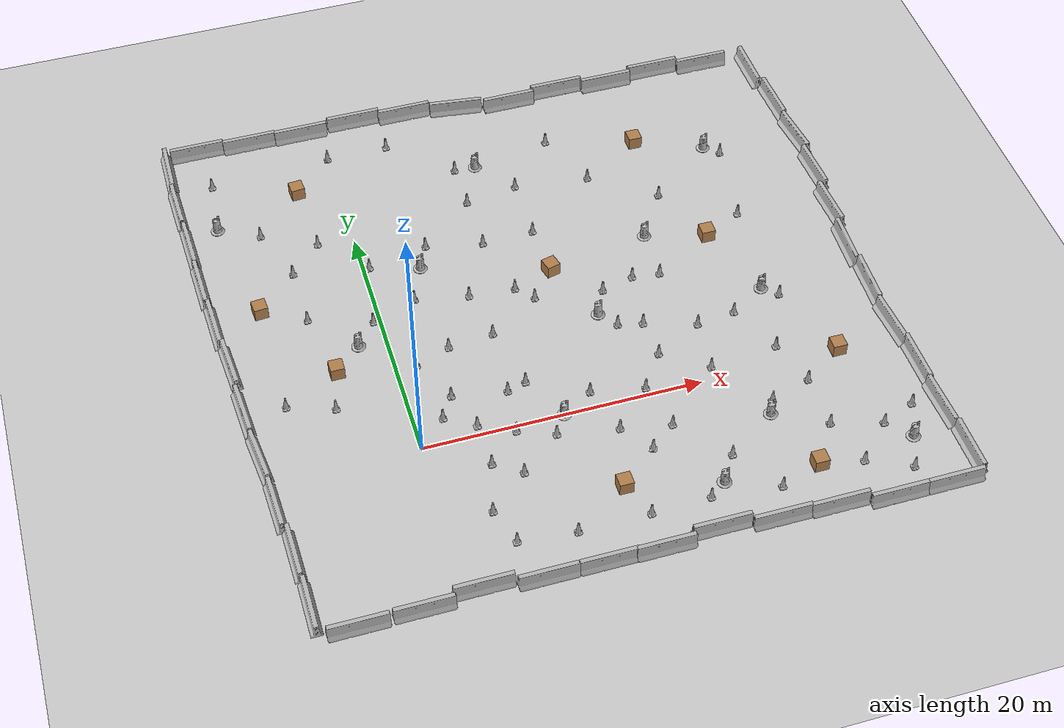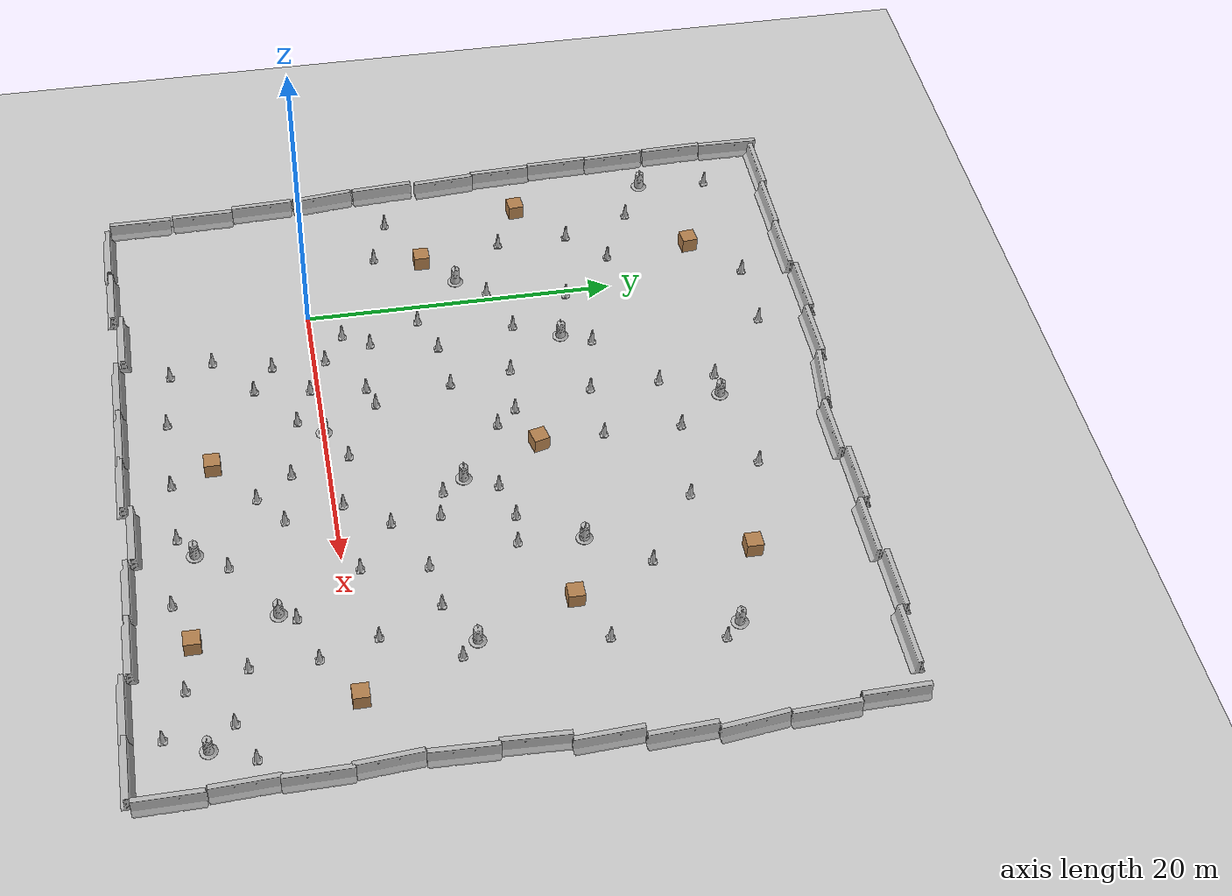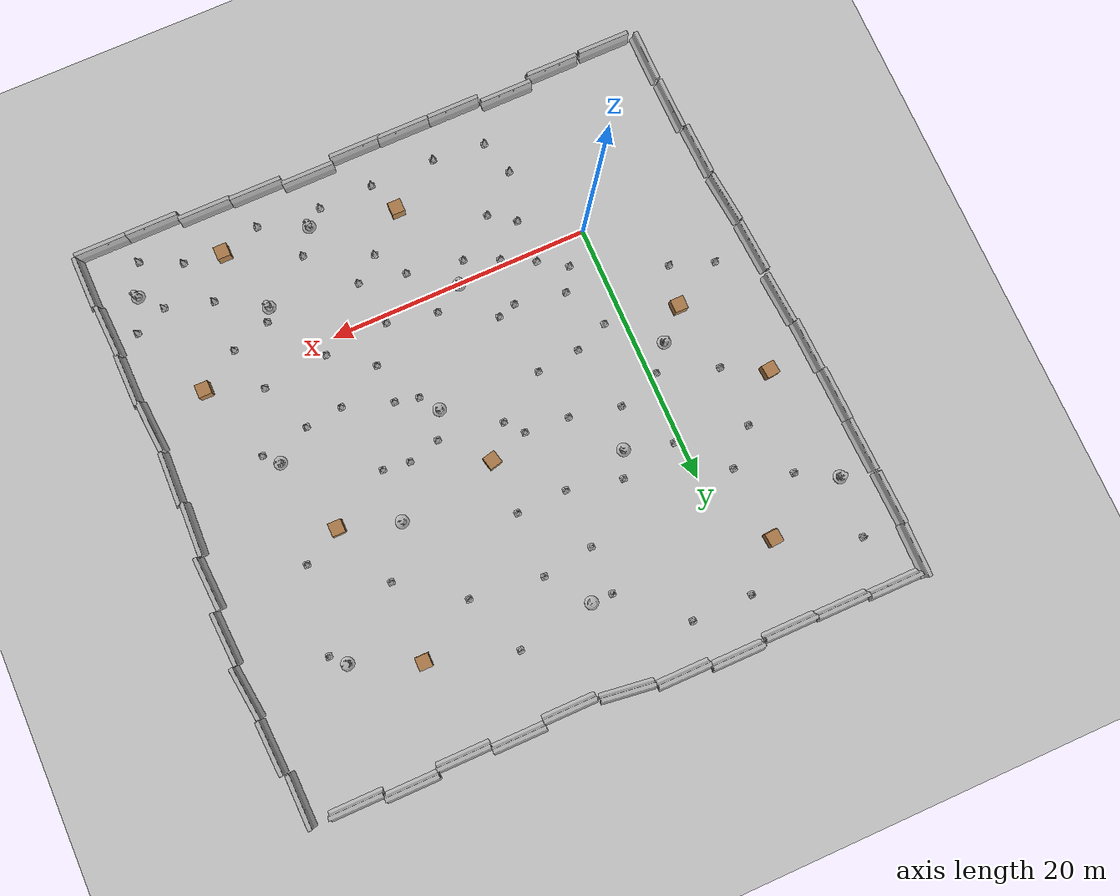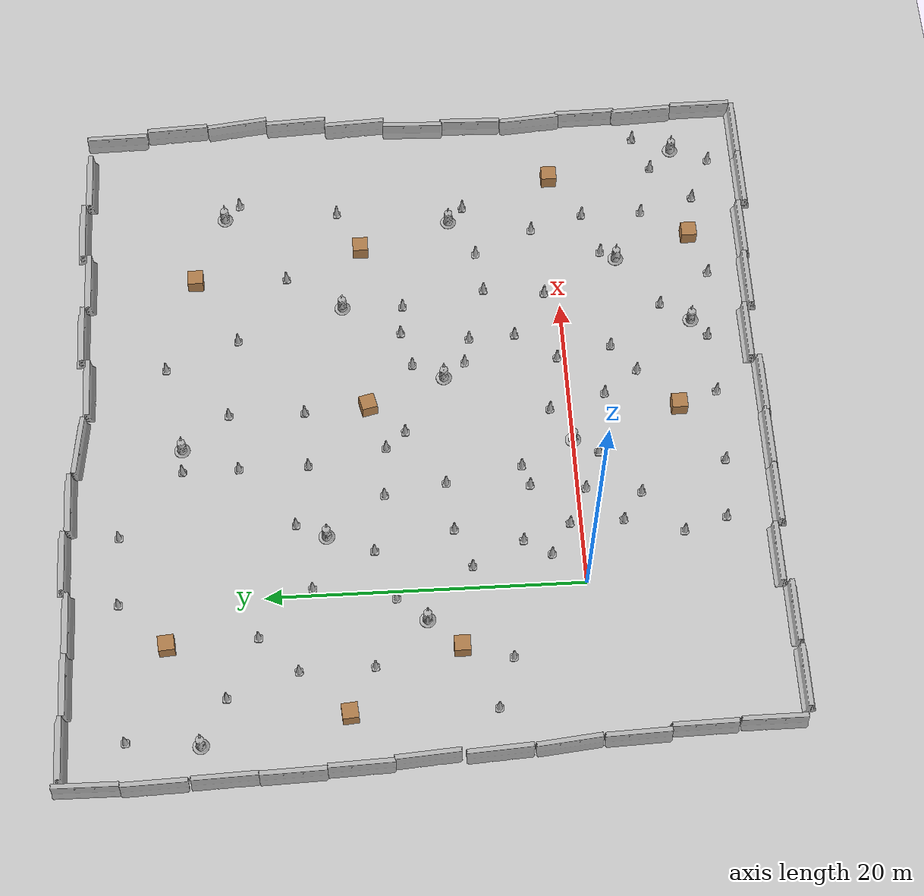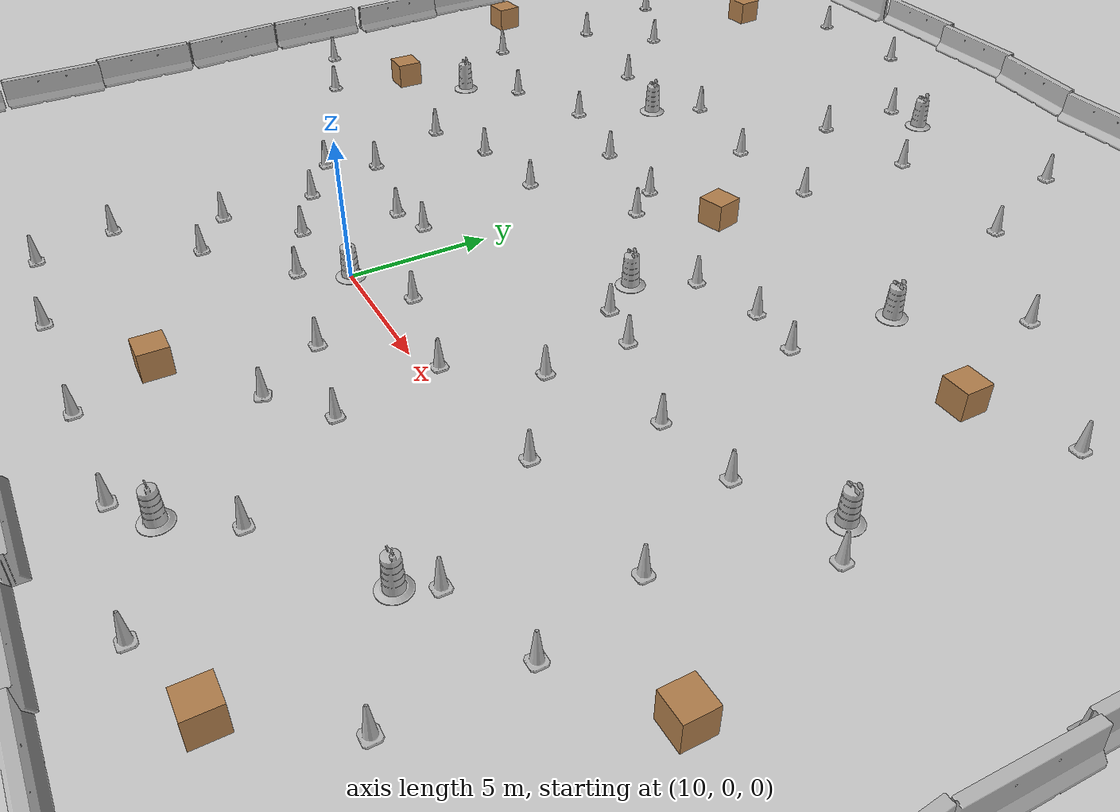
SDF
<sdf version="1.4">
 <world name="default">
  <light name="sun" type="directional">
   <pose>0 0 10 0 -0 0</pose>
   <diffuse>0.8 0.8 0.8 1</diffuse>
   <specular>0.2 0.2 0.2 1</specular>
   <attenuation>
    <range>1000</range>
    <constant>0.9</constant>
    <linear>0.01</linear>
    <quadratic>0.001</quadratic>
   </attenuation>
   <direction>-0.5 0.1 -0.9</direction>
  </light>
  <model name="ground_plane">
   <static>1</static>
   <link name="link">
    <collision name="collision">
     <geometry><plane><normal>0 0 1</normal><size>100 100</size></plane></geometry>
     <surface><friction><ode><mu>100</mu><mu2>50</mu2></ode></friction></surface>
    </collision>
    <visual name="visual">
     <cast_shadows>0</cast_shadows>
     <geometry><plane><normal>0 0 1</normal><size>100 100</size></plane></geometry>
     <material>
      <script><uri>file://media/materials/scripts/gazebo.material</uri><name>Gazebo/Grey</name></script>
     </material>
    </visual>
    <velocity_decay><linear>0</linear><angular>0</angular></velocity_decay>
   </link>
  </model>
  <physics type="ode">
   <max_step_size>0.001</max_step_size>
   <real_time_factor>1</real_time_factor>
   <real_time_update_rate>1000</real_time_update_rate>
   <gravity>0 0 -9.8</gravity>
  </physics>
  <scene><ambient>0.4 0.4 0.4 1</ambient><background>0.7 0.7 0.7 1</background><shadows>1</shadows></scene>
  <spherical_coordinates>
   <surface_model>EARTH_WGS84</surface_model>
   <latitude_deg>0</latitude_deg>
   <longitude_deg>0</longitude_deg>
   <elevation>0</elevation>
   <heading_deg>0</heading_deg>
  </spherical_coordinates>
  <model name="unit_box_1">
   <pose>-3 26 0.5 0 -0 0.083754</pose>
   <link name="link">
    <inertial>
     <mass>1</mass>
     <inertia><ixx>1</ixx><ixy>0</ixy><ixz>0</ixz><iyy>1</iyy><iyz>0</iyz><izz>1</izz></inertia>
    </inertial>
    <collision name="collision"><geometry><box><size>1 1 1</size></box></geometry></collision>
    <visual name="visual">
     <geometry><box><size>1 1 1</size></box></geometry>
     <material>
      <script><uri>file://media/materials/scripts/gazebo.material</uri><name>Gazebo/Wood</name></script>
     </material>
    </visual>
    <velocity_decay><linear>0</linear><angular>0</angular></velocity_decay>
   </link>
   <static>0</static>
  </model>
  <model name="unit_box_3">
   <pose>-8 15 0.5 0 -0 0.083754</pose>
   <link name="link">
    <inertial>
     <mass>1</mass>
     <inertia><ixx>1</ixx><ixy>0</ixy><ixz>0</ixz><iyy>1</iyy><iyz>0</iyz><izz>1</izz></inertia>
    </inertial>
    <collision name="collision"><geometry><box><size>1 1 1</size></box></geometry></collision>
    <visual name="visual">
     <geometry><box><size>1 1 1</size></box></geometry>
     <material>
      <script><uri>file://media/materials/scripts/gazebo.material</uri><name>Gazebo/Wood</name></script>
     </material>
    </visual>
    <velocity_decay><linear>0</linear><angular>0</angular></velocity_decay>
   </link>
   <static>0</static>
  </model>
  <model name="jersey_barrier">
   <static>1</static>
   <link name="link">
    <visual name="visual">
     <geometry><mesh><uri>model://jersey_barrier/meshes/jersey_barrier.dae</uri></mesh></geometry>
    </visual>
    <collision name="upright">
     <pose>0 0 0.5715 0 -0 0</pose>
     <geometry><box><size>4.06542 0.3063 1.143</size></box></geometry>
    </collision>
    <collision name="base">
     <pose>0 0 0.032258 0 -0 0</pose>
     <geometry><box><size>4.06542 0.8107 0.064516</size></box></geometry>
    </collision>
    <collision name="base2">
     <pose>0 0 0.1 0 -0 0</pose>
     <geometry><box><size>4.06542 0.65 0.1</size></box></geometry>
    </collision>
    <collision name="base3">
     <pose>0 0 0.2 0 -0 0</pose>
     <geometry><box><size>4.06542 0.5 0.1</size></box></geometry>
    </collision>
    <collision name="left-angle">
     <pose>0 -0.224 0.2401 0.9 -0 0</pose>
     <geometry><box><size>4.06542 0.5 0.064516</size></box></geometry>
    </collision>
    <collision name="right-angle">
     <pose>0 0.224 0.2401 -0.9 0 0</pose>
     <geometry><box><size>4.06542 0.5 0.064516</size></box></geometry>
    </collision>
    <velocity_decay><linear>0</linear><angular>0</angular></velocity_decay>
   </link>
   <pose>-7.26215 -12.5985 0 0 -0 0</pose>
  </model>
  <model name="jersey_barrier_0">
   <static>1</static>
   <link name="link">
    <visual name="visual">
     <geometry><mesh><uri>model://jersey_barrier/meshes/jersey_barrier.dae</uri></mesh></geometry>
    </visual>
    <collision name="upright">
     <pose>0 0 0.5715 0 -0 0</pose>
     <geometry><box><size>4.06542 0.3063 1.143</size></box></geometry>
    </collision>
    <collision name="base">
     <pose>0 0 0.032258 0 -0 0</pose>
     <geometry><box><size>4.06542 0.8107 0.064516</size></box></geometry>
    </collision>
    <collision name="base2">
     <pose>0 0 0.1 0 -0 0</pose>
     <geometry><box><size>4.06542 0.65 0.1</size></box></geometry>
    </collision>
    <collision name="base3">
     <pose>0 0 0.2 0 -0 0</pose>
     <geometry><box><size>4.06542 0.5 0.1</size></box></geometry>
    </collision>
    <collision name="left-angle">
     <pose>0 -0.224 0.2401 0.9 -0 0</pose>
     <geometry><box><size>4.06542 0.5 0.064516</size></box></geometry>
    </collision>
    <collision name="right-angle">
     <pose>0 0.224 0.2401 -0.9 0 0</pose>
     <geometry><box><size>4.06542 0.5 0.064516</size></box></geometry>
    </collision>
    <velocity_decay><linear>0</linear><angular>0</angular></velocity_decay>
   </link>
   <pose>-3 -12.5184 0 0 -0 0</pose>
  </model>
  <model name="jersey_barrier_1">
   <static>1</static>
   <link name="link">
    <visual name="visual">
     <geometry><mesh><uri>model://jersey_barrier/meshes/jersey_barrier.dae</uri></mesh></geometry>
    </visual>
    <collision name="upright">
     <pose>0 0 0.5715 0 -0 0</pose>
     <geometry><box><size>4.06542 0.3063 1.143</size></box></geometry>
    </collision>
    <collision name="base">
     <pose>0 0 0.032258 0 -0 0</pose>
     <geometry><box><size>4.06542 0.8107 0.064516</size></box></geometry>
    </collision>
    <collision name="base2">
     <pose>0 0 0.1 0 -0 0</pose>
     <geometry><box><size>4.06542 0.65 0.1</size></box></geometry>
    </collision>
    <collision name="base3">
     <pose>0 0 0.2 0 -0 0</pose>
     <geometry><box><size>4.06542 0.5 0.1</size></box></geometry>
    </collision>
    <collision name="left-angle">
     <pose>0 -0.224 0.2401 0.9 -0 0</pose>
     <geometry><box><size>4.06542 0.5 0.064516</size></box></geometry>
    </collision>
    <collision name="right-angle">
     <pose>0 0.224 0.2401 -0.9 0 0</pose>
     <geometry><box><size>4.06542 0.5 0.064516</size></box></geometry>
    </collision>
    <velocity_decay><linear>0</linear><angular>0</angular></velocity_decay>
   </link>
   <pose>1 -12 0 0 -0 0</pose>
  </model>
  <model name="jersey_barrier_2">
   <static>1</static>
   <link name="link">
    <visual name="visual">
     <geometry><mesh><uri>model://jersey_barrier/meshes/jersey_barrier.dae</uri></mesh></geometry>
    </visual>
    <collision name="upright">
     <pose>0 0 0.5715 0 -0 0</pose>
     <geometry><box><size>4.06542 0.3063 1.143</size></box></geometry>
    </collision>
    <collision name="base">
     <pose>0 0 0.032258 0 -0 0</pose>
     <geometry><box><size>4.06542 0.8107 0.064516</size></box></geometry>
    </collision>
    <collision name="base2">
     <pose>0 0 0.1 0 -0 0</pose>
     <geometry><box><size>4.06542 0.65 0.1</size></box></geometry>
    </collision>
    <collision name="base3">
     <pose>0 0 0.2 0 -0 0</pose>
     <geometry><box><size>4.06542 0.5 0.1</size></box></geometry>
    </collision>
    <collision name="left-angle">
     <pose>0 -0.224 0.2401 0.9 -0 0</pose>
     <geometry><box><size>4.06542 0.5 0.064516</size></box></geometry>
    </collision>
    <collision name="right-angle">
     <pose>0 0.224 0.2401 -0.9 0 0</pose>
     <geometry><box><size>4.06542 0.5 0.064516</size></box></geometry>
    </collision>
    <velocity_decay><linear>0</linear><angular>0</angular></velocity_decay>
   </link>
   <pose>5.13642 -12.451 0 0 -0 0</pose>
  </model>
  <model name="jersey_barrier_3">
   <static>1</static>
   <link name="link">
    <visual name="visual">
     <geometry><mesh><uri>model://jersey_barrier/meshes/jersey_barrier.dae</uri></mesh></geometry>
    </visual>
    <collision name="upright">
     <pose>0 0 0.5715 0 -0 0</pose>
     <geometry><box><size>4.06542 0.3063 1.143</size></box></geometry>
    </collision>
    <collision name="base">
     <pose>0 0 0.032258 0 -0 0</pose>
     <geometry><box><size>4.06542 0.8107 0.064516</size></box></geometry>
    </collision>
    <collision name="base2">
     <pose>0 0 0.1 0 -0 0</pose>
     <geometry><box><size>4.06542 0.65 0.1</size></box></geometry>
    </collision>
    <collision name="base3">
     <pose>0 0 0.2 0 -0 0</pose>
     <geometry><box><size>4.06542 0.5 0.1</size></box></geometry>
    </collision>
    <collision name="left-angle">
     <pose>0 -0.224 0.2401 0.9 -0 0</pose>
     <geometry><box><size>4.06542 0.5 0.064516</size></box></geometry>
    </collision>
    <collision name="right-angle">
     <pose>0 0.224 0.2401 -0.9 0 0</pose>
     <geometry><box><size>4.06542 0.5 0.064516</size></box></geometry>
    </collision>
    <velocity_decay><linear>0</linear><angular>0</angular></velocity_decay>
   </link>
   <pose>9.19104 -12.4604 0 0 -0 0</pose>
  </model>
  <model name="jersey_barrier_4">
   <static>1</static>
   <link name="link">
    <visual name="visual">
     <geometry><mesh><uri>model://jersey_barrier/meshes/jersey_barrier.dae</uri></mesh></geometry>
    </visual>
    <collision name="upright">
     <pose>0 0 0.5715 0 -0 0</pose>
     <geometry><box><size>4.06542 0.3063 1.143</size></box></geometry>
    </collision>
    <collision name="base">
     <pose>0 0 0.032258 0 -0 0</pose>
     <geometry><box><size>4.06542 0.8107 0.064516</size></box></geometry>
    </collision>
    <collision name="base2">
     <pose>0 0 0.1 0 -0 0</pose>
     <geometry><box><size>4.06542 0.65 0.1</size></box></geometry>
    </collision>
    <collision name="base3">
     <pose>0 0 0.2 0 -0 0</pose>
     <geometry><box><size>4.06542 0.5 0.1</size></box></geometry>
    </collision>
    <collision name="left-angle">
     <pose>0 -0.224 0.2401 0.9 -0 0</pose>
     <geometry><box><size>4.06542 0.5 0.064516</size></box></geometry>
    </collision>
    <collision name="right-angle">
     <pose>0 0.224 0.2401 -0.9 0 0</pose>
     <geometry><box><size>4.06542 0.5 0.064516</size></box></geometry>
    </collision>
    <velocity_decay><linear>0</linear><angular>0</angular></velocity_decay>
   </link>
   <pose>35.079 -10.8209 0 0 -0 1.58161</pose>
  </model>
  <model name="jersey_barrier_5">
   <static>1</static>
   <link name="link">
    <visual name="visual">
     <geometry><mesh><uri>model://jersey_barrier/meshes/jersey_barrier.dae</uri></mesh></geometry>
    </visual>
    <collision name="upright">
     <pose>0 0 0.5715 0 -0 0</pose>
     <geometry><box><size>4.06542 0.3063 1.143</size></box></geometry>
    </collision>
    <collision name="base">
     <pose>0 0 0.032258 0 -0 0</pose>
     <geometry><box><size>4.06542 0.8107 0.064516</size></box></geometry>
    </collision>
    <collision name="base2">
     <pose>0 0 0.1 0 -0 0</pose>
     <geometry><box><size>4.06542 0.65 0.1</size></box></geometry>
    </collision>
    <collision name="base3">
     <pose>0 0 0.2 0 -0 0</pose>
     <geometry><box><size>4.06542 0.5 0.1</size></box></geometry>
    </collision>
    <collision name="left-angle">
     <pose>0 -0.224 0.2401 0.9 -0 0</pose>
     <geometry><box><size>4.06542 0.5 0.064516</size></box></geometry>
    </collision>
    <collision name="right-angle">
     <pose>0 0.224 0.2401 -0.9 0 0</pose>
     <geometry><box><size>4.06542 0.5 0.064516</size></box></geometry>
    </collision>
    <velocity_decay><linear>0</linear><angular>0</angular></velocity_decay>
   </link>
   <pose>-9.43035 32.377 0 0 -0 0</pose>
  </model>
  <model name="jersey_barrier_6">
   <static>1</static>
   <link name="link">
    <visual name="visual">
     <geometry><mesh><uri>model://jersey_barrier/meshes/jersey_barrier.dae</uri></mesh></geometry>
    </visual>
    <collision name="upright">
     <pose>0 0 0.5715 0 -0 0</pose>
     <geometry><box><size>4.06542 0.3063 1.143</size></box></geometry>
    </collision>
    <collision name="base">
     <pose>0 0 0.032258 0 -0 0</pose>
     <geometry><box><size>4.06542 0.8107 0.064516</size></box></geometry>
    </collision>
    <collision name="base2">
     <pose>0 0 0.1 0 -0 0</pose>
     <geometry><box><size>4.06542 0.65 0.1</size></box></geometry>
    </collision>
    <collision name="base3">
     <pose>0 0 0.2 0 -0 0</pose>
     <geometry><box><size>4.06542 0.5 0.1</size></box></geometry>
    </collision>
    <collision name="left-angle">
     <pose>0 -0.224 0.2401 0.9 -0 0</pose>
     <geometry><box><size>4.06542 0.5 0.064516</size></box></geometry>
    </collision>
    <collision name="right-angle">
     <pose>0 0.224 0.2401 -0.9 0 0</pose>
     <geometry><box><size>4.06542 0.5 0.064516</size></box></geometry>
    </collision>
    <velocity_decay><linear>0</linear><angular>0</angular></velocity_decay>
   </link>
   <pose>-5.41368 32.195 0 0 -0 0</pose>
  </model>
  <model name="jersey_barrier_7">
   <static>1</static>
   <link name="link">
    <visual name="visual">
     <geometry><mesh><uri>model://jersey_barrier/meshes/jersey_barrier.dae</uri></mesh></geometry>
    </visual>
    <collision name="upright">
     <pose>0 0 0.5715 0 -0 0</pose>
     <geometry><box><size>4.06542 0.3063 1.143</size></box></geometry>
    </collision>
    <collision name="base">
     <pose>0 0 0.032258 0 -0 0</pose>
     <geometry><box><size>4.06542 0.8107 0.064516</size></box></geometry>
    </collision>
    <collision name="base2">
     <pose>0 0 0.1 0 -0 0</pose>
     <geometry><box><size>4.06542 0.65 0.1</size></box></geometry>
    </collision>
    <collision name="base3">
     <pose>0 0 0.2 0 -0 0</pose>
     <geometry><box><size>4.06542 0.5 0.1</size></box></geometry>
    </collision>
    <collision name="left-angle">
     <pose>0 -0.224 0.2401 0.9 -0 0</pose>
     <geometry><box><size>4.06542 0.5 0.064516</size></box></geometry>
    </collision>
    <collision name="right-angle">
     <pose>0 0.224 0.2401 -0.9 0 0</pose>
     <geometry><box><size>4.06542 0.5 0.064516</size></box></geometry>
    </collision>
    <velocity_decay><linear>0</linear><angular>0</angular></velocity_decay>
   </link>
   <pose>-1.41387 32.1048 0 0 -0 0</pose>
  </model>
  <model name="jersey_barrier_8">
   <static>1</static>
   <link name="link">
    <visual name="visual">
     <geometry><mesh><uri>model://jersey_barrier/meshes/jersey_barrier.dae</uri></mesh></geometry>
    </visual>
    <collision name="upright">
     <pose>0 0 0.5715 0 -0 0</pose>
     <geometry><box><size>4.06542 0.3063 1.143</size></box></geometry>
    </collision>
    <collision name="base">
     <pose>0 0 0.032258 0 -0 0</pose>
     <geometry><box><size>4.06542 0.8107 0.064516</size></box></geometry>
    </collision>
    <collision name="base2">
     <pose>0 0 0.1 0 -0 0</pose>
     <geometry><box><size>4.06542 0.65 0.1</size></box></geometry>
    </collision>
    <collision name="base3">
     <pose>0 0 0.2 0 -0 0</pose>
     <geometry><box><size>4.06542 0.5 0.1</size></box></geometry>
    </collision>
    <collision name="left-angle">
     <pose>0 -0.224 0.2401 0.9 -0 0</pose>
     <geometry><box><size>4.06542 0.5 0.064516</size></box></geometry>
    </collision>
    <collision name="right-angle">
     <pose>0 0.224 0.2401 -0.9 0 0</pose>
     <geometry><box><size>4.06542 0.5 0.064516</size></box></geometry>
    </collision>
    <velocity_decay><linear>0</linear><angular>0</angular></velocity_decay>
   </link>
   <pose>2.78467 32.4012 0 0 -0 0</pose>
  </model>
  <model name="jersey_barrier_9">
   <static>1</static>
   <link name="link">
    <visual name="visual">
     <geometry><mesh><uri>model://jersey_barrier/meshes/jersey_barrier.dae</uri></mesh></geometry>
    </visual>
    <collision name="upright">
     <pose>0 0 0.5715 0 -0 0</pose>
     <geometry><box><size>4.06542 0.3063 1.143</size></box></geometry>
    </collision>
    <collision name="base">
     <pose>0 0 0.032258 0 -0 0</pose>
     <geometry><box><size>4.06542 0.8107 0.064516</size></box></geometry>
    </collision>
    <collision name="base2">
     <pose>0 0 0.1 0 -0 0</pose>
     <geometry><box><size>4.06542 0.65 0.1</size></box></geometry>
    </collision>
    <collision name="base3">
     <pose>0 0 0.2 0 -0 0</pose>
     <geometry><box><size>4.06542 0.5 0.1</size></box></geometry>
    </collision>
    <collision name="left-angle">
     <pose>0 -0.224 0.2401 0.9 -0 0</pose>
     <geometry><box><size>4.06542 0.5 0.064516</size></box></geometry>
    </collision>
    <collision name="right-angle">
     <pose>0 0.224 0.2401 -0.9 0 0</pose>
     <geometry><box><size>4.06542 0.5 0.064516</size></box></geometry>
    </collision>
    <velocity_decay><linear>0</linear><angular>0</angular></velocity_decay>
   </link>
   <pose>6.77469 32.0696 0 0 -0 0</pose>
  </model>
  <model name="jersey_barrier_10">
   <static>1</static>
   <link name="link">
    <visual name="visual">
     <geometry><mesh><uri>model://jersey_barrier/meshes/jersey_barrier.dae</uri></mesh></geometry>
    </visual>
    <collision name="upright">
     <pose>0 0 0.5715 0 -0 0</pose>
     <geometry><box><size>4.06542 0.3063 1.143</size></box></geometry>
    </collision>
    <collision name="base">
     <pose>0 0 0.032258 0 -0 0</pose>
     <geometry><box><size>4.06542 0.8107 0.064516</size></box></geometry>
    </collision>
    <collision name="base2">
     <pose>0 0 0.1 0 -0 0</pose>
     <geometry><box><size>4.06542 0.65 0.1</size></box></geometry>
    </collision>
    <collision name="base3">
     <pose>0 0 0.2 0 -0 0</pose>
     <geometry><box><size>4.06542 0.5 0.1</size></box></geometry>
    </collision>
    <collision name="left-angle">
     <pose>0 -0.224 0.2401 0.9 -0 0</pose>
     <geometry><box><size>4.06542 0.5 0.064516</size></box></geometry>
    </collision>
    <collision name="right-angle">
     <pose>0 0.224 0.2401 -0.9 0 0</pose>
     <geometry><box><size>4.06542 0.5 0.064516</size></box></geometry>
    </collision>
    <velocity_decay><linear>0</linear><angular>0</angular></velocity_decay>
   </link>
   <pose>10.8346 31.528 0 0 0 -0.129577</pose>
  </model>
  <model name="jersey_barrier_11">
   <static>1</static>
   <link name="link">
    <visual name="visual">
     <geometry><mesh><uri>model://jersey_barrier/meshes/jersey_barrier.dae</uri></mesh></geometry>
    </visual>
    <collision name="upright">
     <pose>0 0 0.5715 0 -0 0</pose>
     <geometry><box><size>4.06542 0.3063 1.143</size></box></geometry>
    </collision>
    <collision name="base">
     <pose>0 0 0.032258 0 -0 0</pose>
     <geometry><box><size>4.06542 0.8107 0.064516</size></box></geometry>
    </collision>
    <collision name="base2">
     <pose>0 0 0.1 0 -0 0</pose>
     <geometry><box><size>4.06542 0.65 0.1</size></box></geometry>
    </collision>
    <collision name="base3">
     <pose>0 0 0.2 0 -0 0</pose>
     <geometry><box><size>4.06542 0.5 0.1</size></box></geometry>
    </collision>
    <collision name="left-angle">
     <pose>0 -0.224 0.2401 0.9 -0 0</pose>
     <geometry><box><size>4.06542 0.5 0.064516</size></box></geometry>
    </collision>
    <collision name="right-angle">
     <pose>0 0.224 0.2401 -0.9 0 0</pose>
     <geometry><box><size>4.06542 0.5 0.064516</size></box></geometry>
    </collision>
    <velocity_decay><linear>0</linear><angular>0</angular></velocity_decay>
   </link>
   <pose>34.5325 5.07874 0 0 -0 1.54369</pose>
  </model>
  <model name="jersey_barrier_12">
   <static>1</static>
   <link name="link">
    <visual name="visual">
     <geometry><mesh><uri>model://jersey_barrier/meshes/jersey_barrier.dae</uri></mesh></geometry>
    </visual>
    <collision name="upright">
     <pose>0 0 0.5715 0 -0 0</pose>
     <geometry><box><size>4.06542 0.3063 1.143</size></box></geometry>
    </collision>
    <collision name="base">
     <pose>0 0 0.032258 0 -0 0</pose>
     <geometry><box><size>4.06542 0.8107 0.064516</size></box></geometry>
    </collision>
    <collision name="base2">
     <pose>0 0 0.1 0 -0 0</pose>
     <geometry><box><size>4.06542 0.65 0.1</size></box></geometry>
    </collision>
    <collision name="base3">
     <pose>0 0 0.2 0 -0 0</pose>
     <geometry><box><size>4.06542 0.5 0.1</size></box></geometry>
    </collision>
    <collision name="left-angle">
     <pose>0 -0.224 0.2401 0.9 -0 0</pose>
     <geometry><box><size>4.06542 0.5 0.064516</size></box></geometry>
    </collision>
    <collision name="right-angle">
     <pose>0 0.224 0.2401 -0.9 0 0</pose>
     <geometry><box><size>4.06542 0.5 0.064516</size></box></geometry>
    </collision>
    <velocity_decay><linear>0</linear><angular>0</angular></velocity_decay>
   </link>
   <pose>34.5148 0.998685 0 0 -0 1.64825</pose>
  </model>
  <model name="jersey_barrier_13">
   <static>1</static>
   <link name="link">
    <visual name="visual">
     <geometry><mesh><uri>model://jersey_barrier/meshes/jersey_barrier.dae</uri></mesh></geometry>
    </visual>
    <collision name="upright">
     <pose>0 0 0.5715 0 -0 0</pose>
     <geometry><box><size>4.06542 0.3063 1.143</size></box></geometry>
    </collision>
    <collision name="base">
     <pose>0 0 0.032258 0 -0 0</pose>
     <geometry><box><size>4.06542 0.8107 0.064516</size></box></geometry>
    </collision>
    <collision name="base2">
     <pose>0 0 0.1 0 -0 0</pose>
     <geometry><box><size>4.06542 0.65 0.1</size></box></geometry>
    </collision>
    <collision name="base3">
     <pose>0 0 0.2 0 -0 0</pose>
     <geometry><box><size>4.06542 0.5 0.1</size></box></geometry>
    </collision>
    <collision name="left-angle">
     <pose>0 -0.224 0.2401 0.9 -0 0</pose>
     <geometry><box><size>4.06542 0.5 0.064516</size></box></geometry>
    </collision>
    <collision name="right-angle">
     <pose>0 0.224 0.2401 -0.9 0 0</pose>
     <geometry><box><size>4.06542 0.5 0.064516</size></box></geometry>
    </collision>
    <velocity_decay><linear>0</linear><angular>0</angular></velocity_decay>
   </link>
   <pose>34.8236 -2.82804 0 0 -0 1.58545</pose>
  </model>
  <model name="jersey_barrier_14">
   <static>1</static>
   <link name="link">
    <visual name="visual">
     <geometry><mesh><uri>model://jersey_barrier/meshes/jersey_barrier.dae</uri></mesh></geometry>
    </visual>
    <collision name="upright">
     <pose>0 0 0.5715 0 -0 0</pose>
     <geometry><box><size>4.06542 0.3063 1.143</size></box></geometry>
    </collision>
    <collision name="base">
     <pose>0 0 0.032258 0 -0 0</pose>
     <geometry><box><size>4.06542 0.8107 0.064516</size></box></geometry>
    </collision>
    <collision name="base2">
     <pose>0 0 0.1 0 -0 0</pose>
     <geometry><box><size>4.06542 0.65 0.1</size></box></geometry>
    </collision>
    <collision name="base3">
     <pose>0 0 0.2 0 -0 0</pose>
     <geometry><box><size>4.06542 0.5 0.1</size></box></geometry>
    </collision>
    <collision name="left-angle">
     <pose>0 -0.224 0.2401 0.9 -0 0</pose>
     <geometry><box><size>4.06542 0.5 0.064516</size></box></geometry>
    </collision>
    <collision name="right-angle">
     <pose>0 0.224 0.2401 -0.9 0 0</pose>
     <geometry><box><size>4.06542 0.5 0.064516</size></box></geometry>
    </collision>
    <velocity_decay><linear>0</linear><angular>0</angular></velocity_decay>
   </link>
   <pose>34.8267 -6.73094 0 0 -0 1.61742</pose>
  </model>
  <model name="jersey_barrier_15">
   <static>1</static>
   <link name="link">
    <visual name="visual">
     <geometry><mesh><uri>model://jersey_barrier/meshes/jersey_barrier.dae</uri></mesh></geometry>
    </visual>
    <collision name="upright">
     <pose>0 0 0.5715 0 -0 0</pose>
     <geometry><box><size>4.06542 0.3063 1.143</size></box></geometry>
    </collision>
    <collision name="base">
     <pose>0 0 0.032258 0 -0 0</pose>
     <geometry><box><size>4.06542 0.8107 0.064516</size></box></geometry>
    </collision>
    <collision name="base2">
     <pose>0 0 0.1 0 -0 0</pose>
     <geometry><box><size>4.06542 0.65 0.1</size></box></geometry>
    </collision>
    <collision name="base3">
     <pose>0 0 0.2 0 -0 0</pose>
     <geometry><box><size>4.06542 0.5 0.1</size></box></geometry>
    </collision>
    <collision name="left-angle">
     <pose>0 -0.224 0.2401 0.9 -0 0</pose>
     <geometry><box><size>4.06542 0.5 0.064516</size></box></geometry>
    </collision>
    <collision name="right-angle">
     <pose>0 0.224 0.2401 -0.9 0 0</pose>
     <geometry><box><size>4.06542 0.5 0.064516</size></box></geometry>
    </collision>
    <velocity_decay><linear>0</linear><angular>0</angular></velocity_decay>
   </link>
   <pose>-10.907 6.17584 0 0 -0 1.63254</pose>
  </model>
  <model name="jersey_barrier_16">
   <static>1</static>
   <link name="link">
    <visual name="visual">
     <geometry><mesh><uri>model://jersey_barrier/meshes/jersey_barrier.dae</uri></mesh></geometry>
    </visual>
    <collision name="upright">
     <pose>0 0 0.5715 0 -0 0</pose>
     <geometry><box><size>4.06542 0.3063 1.143</size></box></geometry>
    </collision>
    <collision name="base">
     <pose>0 0 0.032258 0 -0 0</pose>
     <geometry><box><size>4.06542 0.8107 0.064516</size></box></geometry>
    </collision>
    <collision name="base2">
     <pose>0 0 0.1 0 -0 0</pose>
     <geometry><box><size>4.06542 0.65 0.1</size></box></geometry>
    </collision>
    <collision name="base3">
     <pose>0 0 0.2 0 -0 0</pose>
     <geometry><box><size>4.06542 0.5 0.1</size></box></geometry>
    </collision>
    <collision name="left-angle">
     <pose>0 -0.224 0.2401 0.9 -0 0</pose>
     <geometry><box><size>4.06542 0.5 0.064516</size></box></geometry>
    </collision>
    <collision name="right-angle">
     <pose>0 0.224 0.2401 -0.9 0 0</pose>
     <geometry><box><size>4.06542 0.5 0.064516</size></box></geometry>
    </collision>
    <velocity_decay><linear>0</linear><angular>0</angular></velocity_decay>
   </link>
   <pose>-10.6126 2.01572 0 0 -0 1.67324</pose>
  </model>
  <model name="jersey_barrier_17">
   <static>1</static>
   <link name="link">
    <visual name="visual">
     <geometry><mesh><uri>model://jersey_barrier/meshes/jersey_barrier.dae</uri></mesh></geometry>
    </visual>
    <collision name="upright">
     <pose>0 0 0.5715 0 -0 0</pose>
     <geometry><box><size>4.06542 0.3063 1.143</size></box></geometry>
    </collision>
    <collision name="base">
     <pose>0 0 0.032258 0 -0 0</pose>
     <geometry><box><size>4.06542 0.8107 0.064516</size></box></geometry>
    </collision>
    <collision name="base2">
     <pose>0 0 0.1 0 -0 0</pose>
     <geometry><box><size>4.06542 0.65 0.1</size></box></geometry>
    </collision>
    <collision name="base3">
     <pose>0 0 0.2 0 -0 0</pose>
     <geometry><box><size>4.06542 0.5 0.1</size></box></geometry>
    </collision>
    <collision name="left-angle">
     <pose>0 -0.224 0.2401 0.9 -0 0</pose>
     <geometry><box><size>4.06542 0.5 0.064516</size></box></geometry>
    </collision>
    <collision name="right-angle">
     <pose>0 0.224 0.2401 -0.9 0 0</pose>
     <geometry><box><size>4.06542 0.5 0.064516</size></box></geometry>
    </collision>
    <velocity_decay><linear>0</linear><angular>0</angular></velocity_decay>
   </link>
   <pose>-10.3644 -2.14271 0 0 -0 1.60702</pose>
  </model>
  <model name="jersey_barrier_18">
   <static>1</static>
   <link name="link">
    <visual name="visual">
     <geometry><mesh><uri>model://jersey_barrier/meshes/jersey_barrier.dae</uri></mesh></geometry>
    </visual>
    <collision name="upright">
     <pose>0 0 0.5715 0 -0 0</pose>
     <geometry><box><size>4.06542 0.3063 1.143</size></box></geometry>
    </collision>
    <collision name="base">
     <pose>0 0 0.032258 0 -0 0</pose>
     <geometry><box><size>4.06542 0.8107 0.064516</size></box></geometry>
    </collision>
    <collision name="base2">
     <pose>0 0 0.1 0 -0 0</pose>
     <geometry><box><size>4.06542 0.65 0.1</size></box></geometry>
    </collision>
    <collision name="base3">
     <pose>0 0 0.2 0 -0 0</pose>
     <geometry><box><size>4.06542 0.5 0.1</size></box></geometry>
    </collision>
    <collision name="left-angle">
     <pose>0 -0.224 0.2401 0.9 -0 0</pose>
     <geometry><box><size>4.06542 0.5 0.064516</size></box></geometry>
    </collision>
    <collision name="right-angle">
     <pose>0 0.224 0.2401 -0.9 0 0</pose>
     <geometry><box><size>4.06542 0.5 0.064516</size></box></geometry>
    </collision>
    <velocity_decay><linear>0</linear><angular>0</angular></velocity_decay>
   </link>
   <pose>-9.98265 -6.18571 0 0 -0 1.58701</pose>
  </model>
  <model name="jersey_barrier_19">
   <static>1</static>
   <link name="link">
    <visual name="visual">
     <geometry><mesh><uri>model://jersey_barrier/meshes/jersey_barrier.dae</uri></mesh></geometry>
    </visual>
    <collision name="upright">
     <pose>0 0 0.5715 0 -0 0</pose>
     <geometry><box><size>4.06542 0.3063 1.143</size></box></geometry>
    </collision>
    <collision name="base">
     <pose>0 0 0.032258 0 -0 0</pose>
     <geometry><box><size>4.06542 0.8107 0.064516</size></box></geometry>
    </collision>
    <collision name="base2">
     <pose>0 0 0.1 0 -0 0</pose>
     <geometry><box><size>4.06542 0.65 0.1</size></box></geometry>
    </collision>
    <collision name="base3">
     <pose>0 0 0.2 0 -0 0</pose>
     <geometry><box><size>4.06542 0.5 0.1</size></box></geometry>
    </collision>
    <collision name="left-angle">
     <pose>0 -0.224 0.2401 0.9 -0 0</pose>
     <geometry><box><size>4.06542 0.5 0.064516</size></box></geometry>
    </collision>
    <collision name="right-angle">
     <pose>0 0.224 0.2401 -0.9 0 0</pose>
     <geometry><box><size>4.06542 0.5 0.064516</size></box></geometry>
    </collision>
    <velocity_decay><linear>0</linear><angular>0</angular></velocity_decay>
   </link>
   <pose>-9.85449 -10.3717 0 0 -0 1.57336</pose>
  </model>
  <model name="jersey_barrier_20">
   <static>1</static>
   <link name="link">
    <visual name="visual">
     <geometry><mesh><uri>model://jersey_barrier/meshes/jersey_barrier.dae</uri></mesh></geometry>
    </visual>
    <collision name="upright">
     <pose>0 0 0.5715 0 -0 0</pose>
     <geometry><box><size>4.06542 0.3063 1.143</size></box></geometry>
    </collision>
    <collision name="base">
     <pose>0 0 0.032258 0 -0 0</pose>
     <geometry><box><size>4.06542 0.8107 0.064516</size></box></geometry>
    </collision>
    <collision name="base2">
     <pose>0 0 0.1 0 -0 0</pose>
     <geometry><box><size>4.06542 0.65 0.1</size></box></geometry>
    </collision>
    <collision name="base3">
     <pose>0 0 0.2 0 -0 0</pose>
     <geometry><box><size>4.06542 0.5 0.1</size></box></geometry>
    </collision>
    <collision name="left-angle">
     <pose>0 -0.224 0.2401 0.9 -0 0</pose>
     <geometry><box><size>4.06542 0.5 0.064516</size></box></geometry>
    </collision>
    <collision name="right-angle">
     <pose>0 0.224 0.2401 -0.9 0 0</pose>
     <geometry><box><size>4.06542 0.5 0.064516</size></box></geometry>
    </collision>
    <velocity_decay><linear>0</linear><angular>0</angular></velocity_decay>
   </link>
   <pose>34.4391 9.02418 0 0 -0 1.53674</pose>
  </model>
  <model name="jersey_barrier_21">
   <static>1</static>
   <link name="link">
    <visual name="visual">
     <geometry><mesh><uri>model://jersey_barrier/meshes/jersey_barrier.dae</uri></mesh></geometry>
    </visual>
    <collision name="upright">
     <pose>0 0 0.5715 0 -0 0</pose>
     <geometry><box><size>4.06542 0.3063 1.143</size></box></geometry>
    </collision>
    <collision name="base">
     <pose>0 0 0.032258 0 -0 0</pose>
     <geometry><box><size>4.06542 0.8107 0.064516</size></box></geometry>
    </collision>
    <collision name="base2">
     <pose>0 0 0.1 0 -0 0</pose>
     <geometry><box><size>4.06542 0.65 0.1</size></box></geometry>
    </collision>
    <collision name="base3">
     <pose>0 0 0.2 0 -0 0</pose>
     <geometry><box><size>4.06542 0.5 0.1</size></box></geometry>
    </collision>
    <collision name="left-angle">
     <pose>0 -0.224 0.2401 0.9 -0 0</pose>
     <geometry><box><size>4.06542 0.5 0.064516</size></box></geometry>
    </collision>
    <collision name="right-angle">
     <pose>0 0.224 0.2401 -0.9 0 0</pose>
     <geometry><box><size>4.06542 0.5 0.064516</size></box></geometry>
    </collision>
    <velocity_decay><linear>0</linear><angular>0</angular></velocity_decay>
   </link>
   <pose>-10.9991 10.488 0 0 -0 1.64124</pose>
  </model>
  <model name="Construction Cone">
   <link name="link">
    <collision name="collision">
     <geometry>
      <mesh><scale>10 10 10</scale><uri>model://construction_cone/meshes/construction_cone.dae</uri></mesh>
     </geometry>
    </collision>
    <visual name="visual">
     <geometry>
      <mesh><scale>10 10 10</scale><uri>model://construction_cone/meshes/construction_cone.dae</uri></mesh>
     </geometry>
    </visual>
    <velocity_decay><linear>0</linear><angular>0</angular></velocity_decay>
    <inertial>
     <inertia><ixx>1</ixx><ixy>0</ixy><ixz>0</ixz><iyy>1</iyy><iyz>0</iyz><izz>1</izz></inertia>
     <mass>1</mass>
    </inertial>
   </link>
   <pose>7.29655 8.31428 -1e-06 0 -1e-06 0</pose>
   <static>0</static>
  </model>
  <model name="Construction Cone_0">
   <link name="link">
    <collision name="collision">
     <geometry>
      <mesh><scale>10 10 10</scale><uri>model://construction_cone/meshes/construction_cone.dae</uri></mesh>
     </geometry>
    </collision>
    <visual name="visual">
     <geometry>
      <mesh><scale>10 10 10</scale><uri>model://construction_cone/meshes/construction_cone.dae</uri></mesh>
     </geometry>
    </visual>
    <velocity_decay><linear>0</linear><angular>0</angular></velocity_decay>
    <inertial>
     <inertia><ixx>1</ixx><ixy>0</ixy><ixz>0</ixz><iyy>1</iyy><iyz>0</iyz><izz>1</izz></inertia>
     <mass>1</mass>
    </inertial>
   </link>
   <pose>19.7333 -6.57949 -1e-06 -1e-06 -2e-06 8.07794e-28</pose>
   <static>0</static>
  </model>
  <model name="Construction Cone_1">
   <link name="link">
    <collision name="collision">
     <geometry>
      <mesh><scale>10 10 10</scale><uri>model://construction_cone/meshes/construction_cone.dae</uri></mesh>
     </geometry>
    </collision>
    <visual name="visual">
     <geometry>
      <mesh><scale>10 10 10</scale><uri>model://construction_cone/meshes/construction_cone.dae</uri></mesh>
     </geometry>
    </visual>
    <velocity_decay><linear>0</linear><angular>0</angular></velocity_decay>
    <inertial>
     <inertia><ixx>1</ixx><ixy>0</ixy><ixz>0</ixz><iyy>1</iyy><iyz>0</iyz><izz>1</izz></inertia>
     <mass>1</mass>
    </inertial>
   </link>
   <pose>17.7633 6.19129 -9e-06 0 -0 0</pose>
   <static>0</static>
  </model>
  <model name="Construction Cone_2">
   <link name="link">
    <collision name="collision">
     <geometry>
      <mesh><scale>10 10 10</scale><uri>model://construction_cone/meshes/construction_cone.dae</uri></mesh>
     </geometry>
    </collision>
    <visual name="visual">
     <geometry>
      <mesh><scale>10 10 10</scale><uri>model://construction_cone/meshes/construction_cone.dae</uri></mesh>
     </geometry>
    </visual>
    <velocity_decay><linear>0</linear><angular>0</angular></velocity_decay>
    <inertial>
     <inertia><ixx>1</ixx><ixy>0</ixy><ixz>0</ixz><iyy>1</iyy><iyz>0</iyz><izz>1</izz></inertia>
     <mass>1</mass>
    </inertial>
   </link>
   <pose>2.80714 13.059 0 1e-06 -0 0</pose>
   <static>0</static>
  </model>
  <model name="Construction Cone_3">
   <link name="link">
    <collision name="collision">
     <geometry>
      <mesh><scale>10 10 10</scale><uri>model://construction_cone/meshes/construction_cone.dae</uri></mesh>
     </geometry>
    </collision>
    <visual name="visual">
     <geometry>
      <mesh><scale>10 10 10</scale><uri>model://construction_cone/meshes/construction_cone.dae</uri></mesh>
     </geometry>
    </visual>
    <velocity_decay><linear>0</linear><angular>0</angular></velocity_decay>
    <inertial>
     <inertia><ixx>1</ixx><ixy>0</ixy><ixz>0</ixz><iyy>1</iyy><iyz>0</iyz><izz>1</izz></inertia>
     <mass>1</mass>
    </inertial>
   </link>
   <pose>4.12286 -2.7008 -0 0 -1e-06 0</pose>
   <static>0</static>
  </model>
  <model name="Construction Cone_4">
   <link name="link">
    <collision name="collision">
     <geometry>
      <mesh><scale>10 10 10</scale><uri>model://construction_cone/meshes/construction_cone.dae</uri></mesh>
     </geometry>
    </collision>
    <visual name="visual">
     <geometry>
      <mesh><scale>10 10 10</scale><uri>model://construction_cone/meshes/construction_cone.dae</uri></mesh>
     </geometry>
    </visual>
    <velocity_decay><linear>0</linear><angular>0</angular></velocity_decay>
    <inertial>
     <inertia><ixx>1</ixx><ixy>0</ixy><ixz>0</ixz><iyy>1</iyy><iyz>0</iyz><izz>1</izz></inertia>
     <mass>1</mass>
    </inertial>
   </link>
   <pose>11.1056 10.7156 -0 1e-06 2e-06 8.07794e-28</pose>
   <static>0</static>
  </model>
  <model name="Construction Cone_5">
   <link name="link">
    <collision name="collision">
     <geometry>
      <mesh><scale>10 10 10</scale><uri>model://construction_cone/meshes/construction_cone.dae</uri></mesh>
     </geometry>
    </collision>
    <visual name="visual">
     <geometry>
      <mesh><scale>10 10 10</scale><uri>model://construction_cone/meshes/construction_cone.dae</uri></mesh>
     </geometry>
    </visual>
    <velocity_decay><linear>0</linear><angular>0</angular></velocity_decay>
    <inertial>
     <inertia><ixx>1</ixx><ixy>0</ixy><ixz>0</ixz><iyy>1</iyy><iyz>0</iyz><izz>1</izz></inertia>
     <mass>1</mass>
    </inertial>
   </link>
   <pose>6.6571 12.2638 -1e-06 1e-06 3e-06 -4.03897e-28</pose>
   <static>0</static>
  </model>
  <model name="Construction Cone_6">
   <link name="link">
    <collision name="collision">
     <geometry>
      <mesh><scale>10 10 10</scale><uri>model://construction_cone/meshes/construction_cone.dae</uri></mesh>
     </geometry>
    </collision>
    <visual name="visual">
     <geometry>
      <mesh><scale>10 10 10</scale><uri>model://construction_cone/meshes/construction_cone.dae</uri></mesh>
     </geometry>
    </visual>
    <velocity_decay><linear>0</linear><angular>0</angular></velocity_decay>
    <inertial>
     <inertia><ixx>1</ixx><ixy>0</ixy><ixz>0</ixz><iyy>1</iyy><iyz>0</iyz><izz>1</izz></inertia>
     <mass>1</mass>
    </inertial>
   </link>
   <pose>-4.93524 13.3394 -2e-06 0 1e-06 0</pose>
   <static>0</static>
  </model>
  <model name="Construction Cone_7">
   <link name="link">
    <collision name="collision">
     <geometry>
      <mesh><scale>10 10 10</scale><uri>model://construction_cone/meshes/construction_cone.dae</uri></mesh>
     </geometry>
    </collision>
    <visual name="visual">
     <geometry>
      <mesh><scale>10 10 10</scale><uri>model://construction_cone/meshes/construction_cone.dae</uri></mesh>
     </geometry>
    </visual>
    <velocity_decay><linear>0</linear><angular>0</angular></velocity_decay>
    <inertial>
     <inertia><ixx>1</ixx><ixy>0</ixy><ixz>0</ixz><iyy>1</iyy><iyz>0</iyz><izz>1</izz></inertia>
     <mass>1</mass>
    </inertial>
   </link>
   <pose>17.1922 -9.4642 -1e-06 -2e-06 -3e-06 0</pose>
   <static>0</static>
  </model>
  <model name="Construction Cone_8">
   <link name="link">
    <collision name="collision">
     <geometry>
      <mesh><scale>10 10 10</scale><uri>model://construction_cone/meshes/construction_cone.dae</uri></mesh>
     </geometry>
    </collision>
    <visual name="visual">
     <geometry>
      <mesh><scale>10 10 10</scale><uri>model://construction_cone/meshes/construction_cone.dae</uri></mesh>
     </geometry>
    </visual>
    <velocity_decay><linear>0</linear><angular>0</angular></velocity_decay>
    <inertial>
     <inertia><ixx>1</ixx><ixy>0</ixy><ixz>0</ixz><iyy>1</iyy><iyz>0</iyz><izz>1</izz></inertia>
     <mass>1</mass>
    </inertial>
   </link>
   <pose>-6.51042 22.4224 -2e-06 -1e-06 -0 -0</pose>
   <static>0</static>
  </model>
  <model name="Construction Cone_9">
   <link name="link">
    <collision name="collision">
     <geometry>
      <mesh><scale>10 10 10</scale><uri>model://construction_cone/meshes/construction_cone.dae</uri></mesh>
     </geometry>
    </collision>
    <visual name="visual">
     <geometry>
      <mesh><scale>10 10 10</scale><uri>model://construction_cone/meshes/construction_cone.dae</uri></mesh>
     </geometry>
    </visual>
    <velocity_decay><linear>0</linear><angular>0</angular></velocity_decay>
    <inertial>
     <inertia><ixx>1</ixx><ixy>0</ixy><ixz>0</ixz><iyy>1</iyy><iyz>0</iyz><izz>1</izz></inertia>
     <mass>1</mass>
    </inertial>
   </link>
   <pose>-4.76601 4.88386 -1e-06 -2e-06 -1e-06 8.07794e-28</pose>
   <static>0</static>
  </model>
  <model name="Construction Cone_10">
   <link name="link">
    <collision name="collision">
     <geometry>
      <mesh><scale>10 10 10</scale><uri>model://construction_cone/meshes/construction_cone.dae</uri></mesh>
     </geometry>
    </collision>
    <visual name="visual">
     <geometry>
      <mesh><scale>10 10 10</scale><uri>model://construction_cone/meshes/construction_cone.dae</uri></mesh>
     </geometry>
    </visual>
    <velocity_decay><linear>0</linear><angular>0</angular></velocity_decay>
    <inertial>
     <inertia><ixx>1</ixx><ixy>0</ixy><ixz>0</ixz><iyy>1</iyy><iyz>0</iyz><izz>1</izz></inertia>
     <mass>1</mass>
    </inertial>
   </link>
   <pose>3.03317 3.70489 -0 0 -1e-06 0</pose>
   <static>0</static>
  </model>
  <model name="Construction Cone_11">
   <link name="link">
    <collision name="collision">
     <geometry>
      <mesh><scale>10 10 10</scale><uri>model://construction_cone/meshes/construction_cone.dae</uri></mesh>
     </geometry>
    </collision>
    <visual name="visual">
     <geometry>
      <mesh><scale>10 10 10</scale><uri>model://construction_cone/meshes/construction_cone.dae</uri></mesh>
     </geometry>
    </visual>
    <velocity_decay><linear>0</linear><angular>0</angular></velocity_decay>
    <inertial>
     <inertia><ixx>1</ixx><ixy>0</ixy><ixz>0</ixz><iyy>1</iyy><iyz>0</iyz><izz>1</izz></inertia>
     <mass>1</mass>
    </inertial>
   </link>
   <pose>12.2625 1.30731 -0 0 -1e-06 0</pose>
   <static>0</static>
  </model>
  <model name="Construction Cone_12">
   <link name="link">
    <collision name="collision">
     <geometry>
      <mesh><scale>10 10 10</scale><uri>model://construction_cone/meshes/construction_cone.dae</uri></mesh>
     </geometry>
    </collision>
    <visual name="visual">
     <geometry>
      <mesh><scale>10 10 10</scale><uri>model://construction_cone/meshes/construction_cone.dae</uri></mesh>
     </geometry>
    </visual>
    <velocity_decay><linear>0</linear><angular>0</angular></velocity_decay>
    <inertial>
     <inertia><ixx>1</ixx><ixy>0</ixy><ixz>0</ixz><iyy>1</iyy><iyz>0</iyz><izz>1</izz></inertia>
     <mass>1</mass>
    </inertial>
   </link>
   <pose>-0.487795 11.8459 -0 0 -1e-06 0</pose>
   <static>0</static>
  </model>
  <model name="Construction Cone_13">
   <link name="link">
    <collision name="collision">
     <geometry>
      <mesh><scale>10 10 10</scale><uri>model://construction_cone/meshes/construction_cone.dae</uri></mesh>
     </geometry>
    </collision>
    <visual name="visual">
     <geometry>
      <mesh><scale>10 10 10</scale><uri>model://construction_cone/meshes/construction_cone.dae</uri></mesh>
     </geometry>
    </visual>
    <velocity_decay><linear>0</linear><angular>0</angular></velocity_decay>
    <inertial>
     <inertia><ixx>1</ixx><ixy>0</ixy><ixz>0</ixz><iyy>1</iyy><iyz>0</iyz><izz>1</izz></inertia>
     <mass>1</mass>
    </inertial>
   </link>
   <pose>24.2957 5.33859 -0 -0 -0 -0</pose>
   <static>0</static>
  </model>
  <model name="Construction Cone_14">
   <link name="link">
    <collision name="collision">
     <geometry>
      <mesh><scale>10 10 10</scale><uri>model://construction_cone/meshes/construction_cone.dae</uri></mesh>
     </geometry>
    </collision>
    <visual name="visual">
     <geometry>
      <mesh><scale>10 10 10</scale><uri>model://construction_cone/meshes/construction_cone.dae</uri></mesh>
     </geometry>
    </visual>
    <velocity_decay><linear>0</linear><angular>0</angular></velocity_decay>
    <inertial>
     <inertia><ixx>1</ixx><ixy>0</ixy><ixz>0</ixz><iyy>1</iyy><iyz>0</iyz><izz>1</izz></inertia>
     <mass>1</mass>
    </inertial>
   </link>
   <pose>6.86653 3.00817 0 0 -0 0</pose>
   <static>0</static>
  </model>
  <model name="Construction Cone_15">
   <link name="link">
    <collision name="collision">
     <geometry>
      <mesh><scale>10 10 10</scale><uri>model://construction_cone/meshes/construction_cone.dae</uri></mesh>
     </geometry>
    </collision>
    <visual name="visual">
     <geometry>
      <mesh><scale>10 10 10</scale><uri>model://construction_cone/meshes/construction_cone.dae</uri></mesh>
     </geometry>
    </visual>
    <velocity_decay><linear>0</linear><angular>0</angular></velocity_decay>
    <inertial>
     <inertia><ixx>1</ixx><ixy>0</ixy><ixz>0</ixz><iyy>1</iyy><iyz>0</iyz><izz>1</izz></inertia>
     <mass>1</mass>
    </inertial>
   </link>
   <pose>3.98191 -9.1742 -6e-06 5e-06 -7e-06 0</pose>
   <static>0</static>
  </model>
  <model name="Construction Cone_16">
   <link name="link">
    <collision name="collision">
     <geometry>
      <mesh><scale>10 10 10</scale><uri>model://construction_cone/meshes/construction_cone.dae</uri></mesh>
     </geometry>
    </collision>
    <visual name="visual">
     <geometry>
      <mesh><scale>10 10 10</scale><uri>model://construction_cone/meshes/construction_cone.dae</uri></mesh>
     </geometry>
    </visual>
    <velocity_decay><linear>0</linear><angular>0</angular></velocity_decay>
    <inertial>
     <inertia><ixx>1</ixx><ixy>0</ixy><ixz>0</ixz><iyy>1</iyy><iyz>0</iyz><izz>1</izz></inertia>
     <mass>1</mass>
    </inertial>
   </link>
   <pose>12.9045 21.9904 0 0 -0 0</pose>
   <static>0</static>
  </model>
  <model name="Construction Cone_17">
   <link name="link">
    <collision name="collision">
     <geometry>
      <mesh><scale>10 10 10</scale><uri>model://construction_cone/meshes/construction_cone.dae</uri></mesh>
     </geometry>
    </collision>
    <visual name="visual">
     <geometry>
      <mesh><scale>10 10 10</scale><uri>model://construction_cone/meshes/construction_cone.dae</uri></mesh>
     </geometry>
    </visual>
    <velocity_decay><linear>0</linear><angular>0</angular></velocity_decay>
    <inertial>
     <inertia><ixx>1</ixx><ixy>0</ixy><ixz>0</ixz><iyy>1</iyy><iyz>0</iyz><izz>1</izz></inertia>
     <mass>1</mass>
    </inertial>
   </link>
   <pose>2 2 -1e-06 -2e-06 -3e-06 0</pose>
   <static>0</static>
  </model>
  <model name="Construction Cone_18">
   <link name="link">
    <collision name="collision">
     <geometry>
      <mesh><scale>10 10 10</scale><uri>model://construction_cone/meshes/construction_cone.dae</uri></mesh>
     </geometry>
    </collision>
    <visual name="visual">
     <geometry>
      <mesh><scale>10 10 10</scale><uri>model://construction_cone/meshes/construction_cone.dae</uri></mesh>
     </geometry>
    </visual>
    <velocity_decay><linear>0</linear><angular>0</angular></velocity_decay>
    <inertial>
     <inertia><ixx>1</ixx><ixy>0</ixy><ixz>0</ixz><iyy>1</iyy><iyz>0</iyz><izz>1</izz></inertia>
     <mass>1</mass>
    </inertial>
   </link>
   <pose>3.14498 -6.43429 -6e-06 -7e-06 0 0</pose>
   <static>0</static>
  </model>
  <model name="Construction Cone_19">
   <link name="link">
    <collision name="collision">
     <geometry>
      <mesh><scale>10 10 10</scale><uri>model://construction_cone/meshes/construction_cone.dae</uri></mesh>
     </geometry>
    </collision>
    <visual name="visual">
     <geometry>
      <mesh><scale>10 10 10</scale><uri>model://construction_cone/meshes/construction_cone.dae</uri></mesh>
     </geometry>
    </visual>
    <velocity_decay><linear>0</linear><angular>0</angular></velocity_decay>
    <inertial>
     <inertia><ixx>1</ixx><ixy>0</ixy><ixz>0</ixz><iyy>1</iyy><iyz>0</iyz><izz>1</izz></inertia>
     <mass>1</mass>
    </inertial>
   </link>
   <pose>13.2345 -2.31374 0 0 1e-06 0</pose>
   <static>0</static>
  </model>
  <model name="Construction Cone_20">
   <link name="link">
    <collision name="collision">
     <geometry>
      <mesh><scale>10 10 10</scale><uri>model://construction_cone/meshes/construction_cone.dae</uri></mesh>
     </geometry>
    </collision>
    <visual name="visual">
     <geometry>
      <mesh><scale>10 10 10</scale><uri>model://construction_cone/meshes/construction_cone.dae</uri></mesh>
     </geometry>
    </visual>
    <velocity_decay><linear>0</linear><angular>0</angular></velocity_decay>
    <inertial>
     <inertia><ixx>1</ixx><ixy>0</ixy><ixz>0</ixz><iyy>1</iyy><iyz>0</iyz><izz>1</izz></inertia>
     <mass>1</mass>
    </inertial>
   </link>
   <pose>1.42672 7 -0 0 -1e-06 0</pose>
   <static>0</static>
  </model>
  <model name="Construction Cone_21">
   <link name="link">
    <collision name="collision">
     <geometry>
      <mesh><scale>10 10 10</scale><uri>model://construction_cone/meshes/construction_cone.dae</uri></mesh>
     </geometry>
    </collision>
    <visual name="visual">
     <geometry>
      <mesh><scale>10 10 10</scale><uri>model://construction_cone/meshes/construction_cone.dae</uri></mesh>
     </geometry>
    </visual>
    <velocity_decay><linear>0</linear><angular>0</angular></velocity_decay>
    <inertial>
     <inertia><ixx>1</ixx><ixy>0</ixy><ixz>0</ixz><iyy>1</iyy><iyz>0</iyz><izz>1</izz></inertia>
     <mass>1</mass>
    </inertial>
   </link>
   <pose>6.47202 -0.495356 -9e-06 0 1e-06 0</pose>
   <static>0</static>
  </model>
  <model name="Construction Cone_22">
   <link name="link">
    <collision name="collision">
     <geometry>
      <mesh><scale>10 10 10</scale><uri>model://construction_cone/meshes/construction_cone.dae</uri></mesh>
     </geometry>
    </collision>
    <visual name="visual">
     <geometry>
      <mesh><scale>10 10 10</scale><uri>model://construction_cone/meshes/construction_cone.dae</uri></mesh>
     </geometry>
    </visual>
    <velocity_decay><linear>0</linear><angular>0</angular></velocity_decay>
    <inertial>
     <inertia><ixx>1</ixx><ixy>0</ixy><ixz>0</ixz><iyy>1</iyy><iyz>0</iyz><izz>1</izz></inertia>
     <mass>1</mass>
    </inertial>
   </link>
   <pose>6 -4 -9e-06 -1e-06 2e-06 -8.07794e-28</pose>
   <static>0</static>
  </model>
  <model name="Construction Cone_23">
   <link name="link">
    <collision name="collision">
     <geometry>
      <mesh><scale>10 10 10</scale><uri>model://construction_cone/meshes/construction_cone.dae</uri></mesh>
     </geometry>
    </collision>
    <visual name="visual">
     <geometry>
      <mesh><scale>10 10 10</scale><uri>model://construction_cone/meshes/construction_cone.dae</uri></mesh>
     </geometry>
    </visual>
    <velocity_decay><linear>0</linear><angular>0</angular></velocity_decay>
    <inertial>
     <inertia><ixx>1</ixx><ixy>0</ixy><ixz>0</ixz><iyy>1</iyy><iyz>0</iyz><izz>1</izz></inertia>
     <mass>1</mass>
    </inertial>
   </link>
   <pose>4.05878 0.703394 -0 0 -1e-06 0</pose>
   <static>0</static>
  </model>
  <model name="jersey_barrier_22">
   <static>1</static>
   <link name="link">
    <visual name="visual">
     <geometry><mesh><uri>model://jersey_barrier/meshes/jersey_barrier.dae</uri></mesh></geometry>
    </visual>
    <collision name="upright">
     <pose>0 0 0.5715 0 -0 0</pose>
     <geometry><box><size>4.06542 0.3063 1.143</size></box></geometry>
    </collision>
    <collision name="base">
     <pose>0 0 0.032258 0 -0 0</pose>
     <geometry><box><size>4.06542 0.8107 0.064516</size></box></geometry>
    </collision>
    <collision name="base2">
     <pose>0 0 0.1 0 -0 0</pose>
     <geometry><box><size>4.06542 0.65 0.1</size></box></geometry>
    </collision>
    <collision name="base3">
     <pose>0 0 0.2 0 -0 0</pose>
     <geometry><box><size>4.06542 0.5 0.1</size></box></geometry>
    </collision>
    <collision name="left-angle">
     <pose>0 -0.224 0.2401 0.9 -0 0</pose>
     <geometry><box><size>4.06542 0.5 0.064516</size></box></geometry>
    </collision>
    <collision name="right-angle">
     <pose>0 0.224 0.2401 -0.9 0 0</pose>
     <geometry><box><size>4.06542 0.5 0.064516</size></box></geometry>
    </collision>
    <velocity_decay><linear>0</linear><angular>0</angular></velocity_decay>
   </link>
   <pose>-11.8547 30.7836 0 0 0 -1.58119</pose>
  </model>
  <model name="jersey_barrier_23">
   <static>1</static>
   <link name="link">
    <visual name="visual">
     <geometry><mesh><uri>model://jersey_barrier/meshes/jersey_barrier.dae</uri></mesh></geometry>
    </visual>
    <collision name="upright">
     <pose>0 0 0.5715 0 -0 0</pose>
     <geometry><box><size>4.06542 0.3063 1.143</size></box></geometry>
    </collision>
    <collision name="base">
     <pose>0 0 0.032258 0 -0 0</pose>
     <geometry><box><size>4.06542 0.8107 0.064516</size></box></geometry>
    </collision>
    <collision name="base2">
     <pose>0 0 0.1 0 -0 0</pose>
     <geometry><box><size>4.06542 0.65 0.1</size></box></geometry>
    </collision>
    <collision name="base3">
     <pose>0 0 0.2 0 -0 0</pose>
     <geometry><box><size>4.06542 0.5 0.1</size></box></geometry>
    </collision>
    <collision name="left-angle">
     <pose>0 -0.224 0.2401 0.9 -0 0</pose>
     <geometry><box><size>4.06542 0.5 0.064516</size></box></geometry>
    </collision>
    <collision name="right-angle">
     <pose>0 0.224 0.2401 -0.9 0 0</pose>
     <geometry><box><size>4.06542 0.5 0.064516</size></box></geometry>
    </collision>
    <velocity_decay><linear>0</linear><angular>0</angular></velocity_decay>
   </link>
   <pose>-11.7126 22.5439 0 0 0 -1.53593</pose>
  </model>
  <model name="jersey_barrier_24">
   <static>1</static>
   <link name="link">
    <visual name="visual">
     <geometry><mesh><uri>model://jersey_barrier/meshes/jersey_barrier.dae</uri></mesh></geometry>
    </visual>
    <collision name="upright">
     <pose>0 0 0.5715 0 -0 0</pose>
     <geometry><box><size>4.06542 0.3063 1.143</size></box></geometry>
    </collision>
    <collision name="base">
     <pose>0 0 0.032258 0 -0 0</pose>
     <geometry><box><size>4.06542 0.8107 0.064516</size></box></geometry>
    </collision>
    <collision name="base2">
     <pose>0 0 0.1 0 -0 0</pose>
     <geometry><box><size>4.06542 0.65 0.1</size></box></geometry>
    </collision>
    <collision name="base3">
     <pose>0 0 0.2 0 -0 0</pose>
     <geometry><box><size>4.06542 0.5 0.1</size></box></geometry>
    </collision>
    <collision name="left-angle">
     <pose>0 -0.224 0.2401 0.9 -0 0</pose>
     <geometry><box><size>4.06542 0.5 0.064516</size></box></geometry>
    </collision>
    <collision name="right-angle">
     <pose>0 0.224 0.2401 -0.9 0 0</pose>
     <geometry><box><size>4.06542 0.5 0.064516</size></box></geometry>
    </collision>
    <velocity_decay><linear>0</linear><angular>0</angular></velocity_decay>
   </link>
   <pose>-11.6255 18.4957 0 0 0 -1.53985</pose>
  </model>
  <model name="jersey_barrier_25">
   <static>1</static>
   <link name="link">
    <visual name="visual">
     <geometry><mesh><uri>model://jersey_barrier/meshes/jersey_barrier.dae</uri></mesh></geometry>
    </visual>
    <collision name="upright">
     <pose>0 0 0.5715 0 -0 0</pose>
     <geometry><box><size>4.06542 0.3063 1.143</size></box></geometry>
    </collision>
    <collision name="base">
     <pose>0 0 0.032258 0 -0 0</pose>
     <geometry><box><size>4.06542 0.8107 0.064516</size></box></geometry>
    </collision>
    <collision name="base2">
     <pose>0 0 0.1 0 -0 0</pose>
     <geometry><box><size>4.06542 0.65 0.1</size></box></geometry>
    </collision>
    <collision name="base3">
     <pose>0 0 0.2 0 -0 0</pose>
     <geometry><box><size>4.06542 0.5 0.1</size></box></geometry>
    </collision>
    <collision name="left-angle">
     <pose>0 -0.224 0.2401 0.9 -0 0</pose>
     <geometry><box><size>4.06542 0.5 0.064516</size></box></geometry>
    </collision>
    <collision name="right-angle">
     <pose>0 0.224 0.2401 -0.9 0 0</pose>
     <geometry><box><size>4.06542 0.5 0.064516</size></box></geometry>
    </collision>
    <velocity_decay><linear>0</linear><angular>0</angular></velocity_decay>
   </link>
   <pose>-11.3694 14.4529 0 0 0 -1.53529</pose>
  </model>
  <model name="jersey_barrier_26">
   <static>1</static>
   <link name="link">
    <visual name="visual">
     <geometry><mesh><uri>model://jersey_barrier/meshes/jersey_barrier.dae</uri></mesh></geometry>
    </visual>
    <collision name="upright">
     <pose>0 0 0.5715 0 -0 0</pose>
     <geometry><box><size>4.06542 0.3063 1.143</size></box></geometry>
    </collision>
    <collision name="base">
     <pose>0 0 0.032258 0 -0 0</pose>
     <geometry><box><size>4.06542 0.8107 0.064516</size></box></geometry>
    </collision>
    <collision name="base2">
     <pose>0 0 0.1 0 -0 0</pose>
     <geometry><box><size>4.06542 0.65 0.1</size></box></geometry>
    </collision>
    <collision name="base3">
     <pose>0 0 0.2 0 -0 0</pose>
     <geometry><box><size>4.06542 0.5 0.1</size></box></geometry>
    </collision>
    <collision name="left-angle">
     <pose>0 -0.224 0.2401 0.9 -0 0</pose>
     <geometry><box><size>4.06542 0.5 0.064516</size></box></geometry>
    </collision>
    <collision name="right-angle">
     <pose>0 0.224 0.2401 -0.9 0 0</pose>
     <geometry><box><size>4.06542 0.5 0.064516</size></box></geometry>
    </collision>
    <velocity_decay><linear>0</linear><angular>0</angular></velocity_decay>
   </link>
   <pose>-11.8963 26.7338 0 0 0 -1.54012</pose>
  </model>
  <model name="jersey_barrier_27">
   <static>1</static>
   <link name="link">
    <visual name="visual">
     <geometry><mesh><uri>model://jersey_barrier/meshes/jersey_barrier.dae</uri></mesh></geometry>
    </visual>
    <collision name="upright">
     <pose>0 0 0.5715 0 -0 0</pose>
     <geometry><box><size>4.06542 0.3063 1.143</size></box></geometry>
    </collision>
    <collision name="base">
     <pose>0 0 0.032258 0 -0 0</pose>
     <geometry><box><size>4.06542 0.8107 0.064516</size></box></geometry>
    </collision>
    <collision name="base2">
     <pose>0 0 0.1 0 -0 0</pose>
     <geometry><box><size>4.06542 0.65 0.1</size></box></geometry>
    </collision>
    <collision name="base3">
     <pose>0 0 0.2 0 -0 0</pose>
     <geometry><box><size>4.06542 0.5 0.1</size></box></geometry>
    </collision>
    <collision name="left-angle">
     <pose>0 -0.224 0.2401 0.9 -0 0</pose>
     <geometry><box><size>4.06542 0.5 0.064516</size></box></geometry>
    </collision>
    <collision name="right-angle">
     <pose>0 0.224 0.2401 -0.9 0 0</pose>
     <geometry><box><size>4.06542 0.5 0.064516</size></box></geometry>
    </collision>
    <velocity_decay><linear>0</linear><angular>0</angular></velocity_decay>
   </link>
   <pose>15 31 0 0 -0 0</pose>
  </model>
  <model name="jersey_barrier_28">
   <static>1</static>
   <link name="link">
    <visual name="visual">
     <geometry><mesh><uri>model://jersey_barrier/meshes/jersey_barrier.dae</uri></mesh></geometry>
    </visual>
    <collision name="upright">
     <pose>0 0 0.5715 0 -0 0</pose>
     <geometry><box><size>4.06542 0.3063 1.143</size></box></geometry>
    </collision>
    <collision name="base">
     <pose>0 0 0.032258 0 -0 0</pose>
     <geometry><box><size>4.06542 0.8107 0.064516</size></box></geometry>
    </collision>
    <collision name="base2">
     <pose>0 0 0.1 0 -0 0</pose>
     <geometry><box><size>4.06542 0.65 0.1</size></box></geometry>
    </collision>
    <collision name="base3">
     <pose>0 0 0.2 0 -0 0</pose>
     <geometry><box><size>4.06542 0.5 0.1</size></box></geometry>
    </collision>
    <collision name="left-angle">
     <pose>0 -0.224 0.2401 0.9 -0 0</pose>
     <geometry><box><size>4.06542 0.5 0.064516</size></box></geometry>
    </collision>
    <collision name="right-angle">
     <pose>0 0.224 0.2401 -0.9 0 0</pose>
     <geometry><box><size>4.06542 0.5 0.064516</size></box></geometry>
    </collision>
    <velocity_decay><linear>0</linear><angular>0</angular></velocity_decay>
   </link>
   <pose>19 31.4056 0 0 -0 0</pose>
  </model>
  <model name="jersey_barrier_29">
   <static>1</static>
   <link name="link">
    <visual name="visual">
     <geometry><mesh><uri>model://jersey_barrier/meshes/jersey_barrier.dae</uri></mesh></geometry>
    </visual>
    <collision name="upright">
     <pose>0 0 0.5715 0 -0 0</pose>
     <geometry><box><size>4.06542 0.3063 1.143</size></box></geometry>
    </collision>
    <collision name="base">
     <pose>0 0 0.032258 0 -0 0</pose>
     <geometry><box><size>4.06542 0.8107 0.064516</size></box></geometry>
    </collision>
    <collision name="base2">
     <pose>0 0 0.1 0 -0 0</pose>
     <geometry><box><size>4.06542 0.65 0.1</size></box></geometry>
    </collision>
    <collision name="base3">
     <pose>0 0 0.2 0 -0 0</pose>
     <geometry><box><size>4.06542 0.5 0.1</size></box></geometry>
    </collision>
    <collision name="left-angle">
     <pose>0 -0.224 0.2401 0.9 -0 0</pose>
     <geometry><box><size>4.06542 0.5 0.064516</size></box></geometry>
    </collision>
    <collision name="right-angle">
     <pose>0 0.224 0.2401 -0.9 0 0</pose>
     <geometry><box><size>4.06542 0.5 0.064516</size></box></geometry>
    </collision>
    <velocity_decay><linear>0</linear><angular>0</angular></velocity_decay>
   </link>
   <pose>23 31 0 0 -0 0</pose>
  </model>
  <model name="jersey_barrier_30">
   <static>1</static>
   <link name="link">
    <visual name="visual">
     <geometry><mesh><uri>model://jersey_barrier/meshes/jersey_barrier.dae</uri></mesh></geometry>
    </visual>
    <collision name="upright">
     <pose>0 0 0.5715 0 -0 0</pose>
     <geometry><box><size>4.06542 0.3063 1.143</size></box></geometry>
    </collision>
    <collision name="base">
     <pose>0 0 0.032258 0 -0 0</pose>
     <geometry><box><size>4.06542 0.8107 0.064516</size></box></geometry>
    </collision>
    <collision name="base2">
     <pose>0 0 0.1 0 -0 0</pose>
     <geometry><box><size>4.06542 0.65 0.1</size></box></geometry>
    </collision>
    <collision name="base3">
     <pose>0 0 0.2 0 -0 0</pose>
     <geometry><box><size>4.06542 0.5 0.1</size></box></geometry>
    </collision>
    <collision name="left-angle">
     <pose>0 -0.224 0.2401 0.9 -0 0</pose>
     <geometry><box><size>4.06542 0.5 0.064516</size></box></geometry>
    </collision>
    <collision name="right-angle">
     <pose>0 0.224 0.2401 -0.9 0 0</pose>
     <geometry><box><size>4.06542 0.5 0.064516</size></box></geometry>
    </collision>
    <velocity_decay><linear>0</linear><angular>0</angular></velocity_decay>
   </link>
   <pose>27 31.4215 0 0 -0 0</pose>
  </model>
  <model name="jersey_barrier_31">
   <static>1</static>
   <link name="link">
    <visual name="visual">
     <geometry><mesh><uri>model://jersey_barrier/meshes/jersey_barrier.dae</uri></mesh></geometry>
    </visual>
    <collision name="upright">
     <pose>0 0 0.5715 0 -0 0</pose>
     <geometry><box><size>4.06542 0.3063 1.143</size></box></geometry>
    </collision>
    <collision name="base">
     <pose>0 0 0.032258 0 -0 0</pose>
     <geometry><box><size>4.06542 0.8107 0.064516</size></box></geometry>
    </collision>
    <collision name="base2">
     <pose>0 0 0.1 0 -0 0</pose>
     <geometry><box><size>4.06542 0.65 0.1</size></box></geometry>
    </collision>
    <collision name="base3">
     <pose>0 0 0.2 0 -0 0</pose>
     <geometry><box><size>4.06542 0.5 0.1</size></box></geometry>
    </collision>
    <collision name="left-angle">
     <pose>0 -0.224 0.2401 0.9 -0 0</pose>
     <geometry><box><size>4.06542 0.5 0.064516</size></box></geometry>
    </collision>
    <collision name="right-angle">
     <pose>0 0.224 0.2401 -0.9 0 0</pose>
     <geometry><box><size>4.06542 0.5 0.064516</size></box></geometry>
    </collision>
    <velocity_decay><linear>0</linear><angular>0</angular></velocity_decay>
   </link>
   <pose>31 31 0 0 -0 0</pose>
  </model>
  <model name="jersey_barrier_32">
   <static>1</static>
   <link name="link">
    <visual name="visual">
     <geometry><mesh><uri>model://jersey_barrier/meshes/jersey_barrier.dae</uri></mesh></geometry>
    </visual>
    <collision name="upright">
     <pose>0 0 0.5715 0 -0 0</pose>
     <geometry><box><size>4.06542 0.3063 1.143</size></box></geometry>
    </collision>
    <collision name="base">
     <pose>0 0 0.032258 0 -0 0</pose>
     <geometry><box><size>4.06542 0.8107 0.064516</size></box></geometry>
    </collision>
    <collision name="base2">
     <pose>0 0 0.1 0 -0 0</pose>
     <geometry><box><size>4.06542 0.65 0.1</size></box></geometry>
    </collision>
    <collision name="base3">
     <pose>0 0 0.2 0 -0 0</pose>
     <geometry><box><size>4.06542 0.5 0.1</size></box></geometry>
    </collision>
    <collision name="left-angle">
     <pose>0 -0.224 0.2401 0.9 -0 0</pose>
     <geometry><box><size>4.06542 0.5 0.064516</size></box></geometry>
    </collision>
    <collision name="right-angle">
     <pose>0 0.224 0.2401 -0.9 0 0</pose>
     <geometry><box><size>4.06542 0.5 0.064516</size></box></geometry>
    </collision>
    <velocity_decay><linear>0</linear><angular>0</angular></velocity_decay>
   </link>
   <pose>13 -12.505 0 0 -0 0</pose>
  </model>
  <model name="jersey_barrier_33">
   <static>1</static>
   <link name="link">
    <visual name="visual">
     <geometry><mesh><uri>model://jersey_barrier/meshes/jersey_barrier.dae</uri></mesh></geometry>
    </visual>
    <collision name="upright">
     <pose>0 0 0.5715 0 -0 0</pose>
     <geometry><box><size>4.06542 0.3063 1.143</size></box></geometry>
    </collision>
    <collision name="base">
     <pose>0 0 0.032258 0 -0 0</pose>
     <geometry><box><size>4.06542 0.8107 0.064516</size></box></geometry>
    </collision>
    <collision name="base2">
     <pose>0 0 0.1 0 -0 0</pose>
     <geometry><box><size>4.06542 0.65 0.1</size></box></geometry>
    </collision>
    <collision name="base3">
     <pose>0 0 0.2 0 -0 0</pose>
     <geometry><box><size>4.06542 0.5 0.1</size></box></geometry>
    </collision>
    <collision name="left-angle">
     <pose>0 -0.224 0.2401 0.9 -0 0</pose>
     <geometry><box><size>4.06542 0.5 0.064516</size></box></geometry>
    </collision>
    <collision name="right-angle">
     <pose>0 0.224 0.2401 -0.9 0 0</pose>
     <geometry><box><size>4.06542 0.5 0.064516</size></box></geometry>
    </collision>
    <velocity_decay><linear>0</linear><angular>0</angular></velocity_decay>
   </link>
   <pose>17 -12 0 0 -0 0</pose>
  </model>
  <model name="jersey_barrier_34">
   <static>1</static>
   <link name="link">
    <visual name="visual">
     <geometry><mesh><uri>model://jersey_barrier/meshes/jersey_barrier.dae</uri></mesh></geometry>
    </visual>
    <collision name="upright">
     <pose>0 0 0.5715 0 -0 0</pose>
     <geometry><box><size>4.06542 0.3063 1.143</size></box></geometry>
    </collision>
    <collision name="base">
     <pose>0 0 0.032258 0 -0 0</pose>
     <geometry><box><size>4.06542 0.8107 0.064516</size></box></geometry>
    </collision>
    <collision name="base2">
     <pose>0 0 0.1 0 -0 0</pose>
     <geometry><box><size>4.06542 0.65 0.1</size></box></geometry>
    </collision>
    <collision name="base3">
     <pose>0 0 0.2 0 -0 0</pose>
     <geometry><box><size>4.06542 0.5 0.1</size></box></geometry>
    </collision>
    <collision name="left-angle">
     <pose>0 -0.224 0.2401 0.9 -0 0</pose>
     <geometry><box><size>4.06542 0.5 0.064516</size></box></geometry>
    </collision>
    <collision name="right-angle">
     <pose>0 0.224 0.2401 -0.9 0 0</pose>
     <geometry><box><size>4.06542 0.5 0.064516</size></box></geometry>
    </collision>
    <velocity_decay><linear>0</linear><angular>0</angular></velocity_decay>
   </link>
   <pose>21 -12.4598 0 0 -0 0</pose>
  </model>
  <model name="jersey_barrier_35">
   <static>1</static>
   <link name="link">
    <visual name="visual">
     <geometry><mesh><uri>model://jersey_barrier/meshes/jersey_barrier.dae</uri></mesh></geometry>
    </visual>
    <collision name="upright">
     <pose>0 0 0.5715 0 -0 0</pose>
     <geometry><box><size>4.06542 0.3063 1.143</size></box></geometry>
    </collision>
    <collision name="base">
     <pose>0 0 0.032258 0 -0 0</pose>
     <geometry><box><size>4.06542 0.8107 0.064516</size></box></geometry>
    </collision>
    <collision name="base2">
     <pose>0 0 0.1 0 -0 0</pose>
     <geometry><box><size>4.06542 0.65 0.1</size></box></geometry>
    </collision>
    <collision name="base3">
     <pose>0 0 0.2 0 -0 0</pose>
     <geometry><box><size>4.06542 0.5 0.1</size></box></geometry>
    </collision>
    <collision name="left-angle">
     <pose>0 -0.224 0.2401 0.9 -0 0</pose>
     <geometry><box><size>4.06542 0.5 0.064516</size></box></geometry>
    </collision>
    <collision name="right-angle">
     <pose>0 0.224 0.2401 -0.9 0 0</pose>
     <geometry><box><size>4.06542 0.5 0.064516</size></box></geometry>
    </collision>
    <velocity_decay><linear>0</linear><angular>0</angular></velocity_decay>
   </link>
   <pose>25 -12.5589 0 0 -0 0</pose>
  </model>
  <model name="jersey_barrier_36">
   <static>1</static>
   <link name="link">
    <visual name="visual">
     <geometry><mesh><uri>model://jersey_barrier/meshes/jersey_barrier.dae</uri></mesh></geometry>
    </visual>
    <collision name="upright">
     <pose>0 0 0.5715 0 -0 0</pose>
     <geometry><box><size>4.06542 0.3063 1.143</size></box></geometry>
    </collision>
    <collision name="base">
     <pose>0 0 0.032258 0 -0 0</pose>
     <geometry><box><size>4.06542 0.8107 0.064516</size></box></geometry>
    </collision>
    <collision name="base2">
     <pose>0 0 0.1 0 -0 0</pose>
     <geometry><box><size>4.06542 0.65 0.1</size></box></geometry>
    </collision>
    <collision name="base3">
     <pose>0 0 0.2 0 -0 0</pose>
     <geometry><box><size>4.06542 0.5 0.1</size></box></geometry>
    </collision>
    <collision name="left-angle">
     <pose>0 -0.224 0.2401 0.9 -0 0</pose>
     <geometry><box><size>4.06542 0.5 0.064516</size></box></geometry>
    </collision>
    <collision name="right-angle">
     <pose>0 0.224 0.2401 -0.9 0 0</pose>
     <geometry><box><size>4.06542 0.5 0.064516</size></box></geometry>
    </collision>
    <velocity_decay><linear>0</linear><angular>0</angular></velocity_decay>
   </link>
   <pose>29 -13 0 0 -0 0</pose>
  </model>
  <model name="jersey_barrier_37">
   <static>1</static>
   <link name="link">
    <visual name="visual">
     <geometry><mesh><uri>model://jersey_barrier/meshes/jersey_barrier.dae</uri></mesh></geometry>
    </visual>
    <collision name="upright">
     <pose>0 0 0.5715 0 -0 0</pose>
     <geometry><box><size>4.06542 0.3063 1.143</size></box></geometry>
    </collision>
    <collision name="base">
     <pose>0 0 0.032258 0 -0 0</pose>
     <geometry><box><size>4.06542 0.8107 0.064516</size></box></geometry>
    </collision>
    <collision name="base2">
     <pose>0 0 0.1 0 -0 0</pose>
     <geometry><box><size>4.06542 0.65 0.1</size></box></geometry>
    </collision>
    <collision name="base3">
     <pose>0 0 0.2 0 -0 0</pose>
     <geometry><box><size>4.06542 0.5 0.1</size></box></geometry>
    </collision>
    <collision name="left-angle">
     <pose>0 -0.224 0.2401 0.9 -0 0</pose>
     <geometry><box><size>4.06542 0.5 0.064516</size></box></geometry>
    </collision>
    <collision name="right-angle">
     <pose>0 0.224 0.2401 -0.9 0 0</pose>
     <geometry><box><size>4.06542 0.5 0.064516</size></box></geometry>
    </collision>
    <velocity_decay><linear>0</linear><angular>0</angular></velocity_decay>
   </link>
   <pose>33 -13 0 0 -0 0</pose>
  </model>
  <model name="jersey_barrier_38">
   <static>1</static>
   <link name="link">
    <visual name="visual">
     <geometry><mesh><uri>model://jersey_barrier/meshes/jersey_barrier.dae</uri></mesh></geometry>
    </visual>
    <collision name="upright">
     <pose>0 0 0.5715 0 -0 0</pose>
     <geometry><box><size>4.06542 0.3063 1.143</size></box></geometry>
    </collision>
    <collision name="base">
     <pose>0 0 0.032258 0 -0 0</pose>
     <geometry><box><size>4.06542 0.8107 0.064516</size></box></geometry>
    </collision>
    <collision name="base2">
     <pose>0 0 0.1 0 -0 0</pose>
     <geometry><box><size>4.06542 0.65 0.1</size></box></geometry>
    </collision>
    <collision name="base3">
     <pose>0 0 0.2 0 -0 0</pose>
     <geometry><box><size>4.06542 0.5 0.1</size></box></geometry>
    </collision>
    <collision name="left-angle">
     <pose>0 -0.224 0.2401 0.9 -0 0</pose>
     <geometry><box><size>4.06542 0.5 0.064516</size></box></geometry>
    </collision>
    <collision name="right-angle">
     <pose>0 0.224 0.2401 -0.9 0 0</pose>
     <geometry><box><size>4.06542 0.5 0.064516</size></box></geometry>
    </collision>
    <velocity_decay><linear>0</linear><angular>0</angular></velocity_decay>
   </link>
   <pose>34.463 29.206 0 0 0 -1.54926</pose>
  </model>
  <model name="jersey_barrier_39">
   <static>1</static>
   <link name="link">
    <visual name="visual">
     <geometry><mesh><uri>model://jersey_barrier/meshes/jersey_barrier.dae</uri></mesh></geometry>
    </visual>
    <collision name="upright">
     <pose>0 0 0.5715 0 -0 0</pose>
     <geometry><box><size>4.06542 0.3063 1.143</size></box></geometry>
    </collision>
    <collision name="base">
     <pose>0 0 0.032258 0 -0 0</pose>
     <geometry><box><size>4.06542 0.8107 0.064516</size></box></geometry>
    </collision>
    <collision name="base2">
     <pose>0 0 0.1 0 -0 0</pose>
     <geometry><box><size>4.06542 0.65 0.1</size></box></geometry>
    </collision>
    <collision name="base3">
     <pose>0 0 0.2 0 -0 0</pose>
     <geometry><box><size>4.06542 0.5 0.1</size></box></geometry>
    </collision>
    <collision name="left-angle">
     <pose>0 -0.224 0.2401 0.9 -0 0</pose>
     <geometry><box><size>4.06542 0.5 0.064516</size></box></geometry>
    </collision>
    <collision name="right-angle">
     <pose>0 0.224 0.2401 -0.9 0 0</pose>
     <geometry><box><size>4.06542 0.5 0.064516</size></box></geometry>
    </collision>
    <velocity_decay><linear>0</linear><angular>0</angular></velocity_decay>
   </link>
   <pose>34.9785 25.1169 0 0 0 -1.52193</pose>
  </model>
  <model name="jersey_barrier_40">
   <static>1</static>
   <link name="link">
    <visual name="visual">
     <geometry><mesh><uri>model://jersey_barrier/meshes/jersey_barrier.dae</uri></mesh></geometry>
    </visual>
    <collision name="upright">
     <pose>0 0 0.5715 0 -0 0</pose>
     <geometry><box><size>4.06542 0.3063 1.143</size></box></geometry>
    </collision>
    <collision name="base">
     <pose>0 0 0.032258 0 -0 0</pose>
     <geometry><box><size>4.06542 0.8107 0.064516</size></box></geometry>
    </collision>
    <collision name="base2">
     <pose>0 0 0.1 0 -0 0</pose>
     <geometry><box><size>4.06542 0.65 0.1</size></box></geometry>
    </collision>
    <collision name="base3">
     <pose>0 0 0.2 0 -0 0</pose>
     <geometry><box><size>4.06542 0.5 0.1</size></box></geometry>
    </collision>
    <collision name="left-angle">
     <pose>0 -0.224 0.2401 0.9 -0 0</pose>
     <geometry><box><size>4.06542 0.5 0.064516</size></box></geometry>
    </collision>
    <collision name="right-angle">
     <pose>0 0.224 0.2401 -0.9 0 0</pose>
     <geometry><box><size>4.06542 0.5 0.064516</size></box></geometry>
    </collision>
    <velocity_decay><linear>0</linear><angular>0</angular></velocity_decay>
   </link>
   <pose>35.1351 17.0134 0 0 0 -1.51848</pose>
  </model>
  <model name="jersey_barrier_41">
   <static>1</static>
   <link name="link">
    <visual name="visual">
     <geometry><mesh><uri>model://jersey_barrier/meshes/jersey_barrier.dae</uri></mesh></geometry>
    </visual>
    <collision name="upright">
     <pose>0 0 0.5715 0 -0 0</pose>
     <geometry><box><size>4.06542 0.3063 1.143</size></box></geometry>
    </collision>
    <collision name="base">
     <pose>0 0 0.032258 0 -0 0</pose>
     <geometry><box><size>4.06542 0.8107 0.064516</size></box></geometry>
    </collision>
    <collision name="base2">
     <pose>0 0 0.1 0 -0 0</pose>
     <geometry><box><size>4.06542 0.65 0.1</size></box></geometry>
    </collision>
    <collision name="base3">
     <pose>0 0 0.2 0 -0 0</pose>
     <geometry><box><size>4.06542 0.5 0.1</size></box></geometry>
    </collision>
    <collision name="left-angle">
     <pose>0 -0.224 0.2401 0.9 -0 0</pose>
     <geometry><box><size>4.06542 0.5 0.064516</size></box></geometry>
    </collision>
    <collision name="right-angle">
     <pose>0 0.224 0.2401 -0.9 0 0</pose>
     <geometry><box><size>4.06542 0.5 0.064516</size></box></geometry>
    </collision>
    <velocity_decay><linear>0</linear><angular>0</angular></velocity_decay>
   </link>
   <pose>35.176 21.0314 0 0 0 -1.44901</pose>
  </model>
  <model name="jersey_barrier_42">
   <static>1</static>
   <link name="link">
    <visual name="visual">
     <geometry><mesh><uri>model://jersey_barrier/meshes/jersey_barrier.dae</uri></mesh></geometry>
    </visual>
    <collision name="upright">
     <pose>0 0 0.5715 0 -0 0</pose>
     <geometry><box><size>4.06542 0.3063 1.143</size></box></geometry>
    </collision>
    <collision name="base">
     <pose>0 0 0.032258 0 -0 0</pose>
     <geometry><box><size>4.06542 0.8107 0.064516</size></box></geometry>
    </collision>
    <collision name="base2">
     <pose>0 0 0.1 0 -0 0</pose>
     <geometry><box><size>4.06542 0.65 0.1</size></box></geometry>
    </collision>
    <collision name="base3">
     <pose>0 0 0.2 0 -0 0</pose>
     <geometry><box><size>4.06542 0.5 0.1</size></box></geometry>
    </collision>
    <collision name="left-angle">
     <pose>0 -0.224 0.2401 0.9 -0 0</pose>
     <geometry><box><size>4.06542 0.5 0.064516</size></box></geometry>
    </collision>
    <collision name="right-angle">
     <pose>0 0.224 0.2401 -0.9 0 0</pose>
     <geometry><box><size>4.06542 0.5 0.064516</size></box></geometry>
    </collision>
    <velocity_decay><linear>0</linear><angular>0</angular></velocity_decay>
   </link>
   <pose>34.8095 13.0043 0 0 0 -1.51745</pose>
  </model>
  <model name="unit_box_2_0">
   <pose>12 -7 0.5 0 -0 0</pose>
   <link name="link">
    <inertial>
     <mass>1</mass>
     <inertia><ixx>1</ixx><ixy>0</ixy><ixz>0</ixz><iyy>1</iyy><iyz>0</iyz><izz>1</izz></inertia>
    </inertial>
    <collision name="collision"><geometry><box><size>1 1 1</size></box></geometry></collision>
    <visual name="visual">
     <geometry><box><size>1 1 1</size></box></geometry>
     <material>
      <script><uri>file://media/materials/scripts/gazebo.material</uri><name>Gazebo/Wood</name></script>
     </material>
    </visual>
    <velocity_decay><linear>0</linear><angular>0</angular></velocity_decay>
   </link>
   <static>0</static>
  </model>
  <model name="unit_box_4">
   <pose>25 -9 0.5 0 -0 0</pose>
   <link name="link">
    <inertial>
     <mass>1</mass>
     <inertia><ixx>1</ixx><ixy>0</ixy><ixz>0</ixz><iyy>1</iyy><iyz>0</iyz><izz>1</izz></inertia>
    </inertial>
    <collision name="collision"><geometry><box><size>1 1 1</size></box></geometry></collision>
    <visual name="visual">
     <geometry><box><size>1 1 1</size></box></geometry>
     <material>
      <script><uri>file://media/materials/scripts/gazebo.material</uri><name>Gazebo/Wood</name></script>
     </material>
    </visual>
    <velocity_decay><linear>0</linear><angular>0</angular></velocity_decay>
   </link>
   <static>0</static>
  </model>
  <model name="unit_box_5">
   <pose>30 0 0.5 0 -0 0</pose>
   <link name="link">
    <inertial>
     <mass>1</mass>
     <inertia><ixx>1</ixx><ixy>0</ixy><ixz>0</ixz><iyy>1</iyy><iyz>0</iyz><izz>1</izz></inertia>
    </inertial>
    <collision name="collision"><geometry><box><size>1 1 1</size></box></geometry></collision>
    <visual name="visual">
     <geometry><box><size>1 1 1</size></box></geometry>
     <material>
      <script><uri>file://media/materials/scripts/gazebo.material</uri><name>Gazebo/Wood</name></script>
     </material>
    </visual>
    <velocity_decay><linear>0</linear><angular>0</angular></velocity_decay>
   </link>
   <static>0</static>
  </model>
  <model name="unit_box_6">
   <pose>25 13 0.5 0 -0 0</pose>
   <link name="link">
    <inertial>
     <mass>1</mass>
     <inertia><ixx>1</ixx><ixy>0</ixy><ixz>0</ixz><iyy>1</iyy><iyz>0</iyz><izz>1</izz></inertia>
    </inertial>
    <collision name="collision"><geometry><box><size>1 1 1</size></box></geometry></collision>
    <visual name="visual">
     <geometry><box><size>1 1 1</size></box></geometry>
     <material>
      <script><uri>file://media/materials/scripts/gazebo.material</uri><name>Gazebo/Wood</name></script>
     </material>
    </visual>
    <velocity_decay><linear>0</linear><angular>0</angular></velocity_decay>
   </link>
   <static>0</static>
  </model>
  <model name="unit_box_7">
   <pose>23 24 0.5 0 -0 0</pose>
   <link name="link">
    <inertial>
     <mass>1</mass>
     <inertia><ixx>1</ixx><ixy>0</ixy><ixz>0</ixz><iyy>1</iyy><iyz>0</iyz><izz>1</izz></inertia>
    </inertial>
    <collision name="collision"><geometry><box><size>1 1 1</size></box></geometry></collision>
    <visual name="visual">
     <geometry><box><size>1 1 1</size></box></geometry>
     <material>
      <script><uri>file://media/materials/scripts/gazebo.material</uri><name>Gazebo/Wood</name></script>
     </material>
    </visual>
    <velocity_decay><linear>0</linear><angular>0</angular></velocity_decay>
   </link>
   <static>0</static>
  </model>
  <model name="unit_box_8">
   <pose>13 13 0.5 0 -0 0.240179</pose>
   <link name="link">
    <inertial>
     <mass>1</mass>
     <inertia><ixx>1</ixx><ixy>0</ixy><ixz>0</ixz><iyy>1</iyy><iyz>0</iyz><izz>1</izz></inertia>
    </inertial>
    <collision name="collision"><geometry><box><size>1 1 1</size></box></geometry></collision>
    <visual name="visual">
     <geometry><box><size>1 1 1</size></box></geometry>
     <material>
      <script><uri>file://media/materials/scripts/gazebo.material</uri><name>Gazebo/Wood</name></script>
     </material>
    </visual>
    <velocity_decay><linear>0</linear><angular>0</angular></velocity_decay>
   </link>
   <static>0</static>
  </model>
  <model name="Construction Cone_24">
   <link name="link">
    <collision name="collision">
     <geometry>
      <mesh><scale>10 10 10</scale><uri>model://construction_cone/meshes/construction_cone.dae</uri></mesh>
     </geometry>
    </collision>
    <visual name="visual">
     <geometry>
      <mesh><scale>10 10 10</scale><uri>model://construction_cone/meshes/construction_cone.dae</uri></mesh>
     </geometry>
    </visual>
    <velocity_decay><linear>0</linear><angular>0</angular></velocity_decay>
    <inertial>
     <inertia><ixx>1</ixx><ixy>0</ixy><ixz>0</ixz><iyy>1</iyy><iyz>0</iyz><izz>1</izz></inertia>
     <mass>1</mass>
    </inertial>
   </link>
   <pose>-2.65659 20.4095 -0 0 -1e-06 0</pose>
   <static>0</static>
  </model>
  <model name="Construction Cone_25">
   <link name="link">
    <collision name="collision">
     <geometry>
      <mesh><scale>10 10 10</scale><uri>model://construction_cone/meshes/construction_cone.dae</uri></mesh>
     </geometry>
    </collision>
    <visual name="visual">
     <geometry>
      <mesh><scale>10 10 10</scale><uri>model://construction_cone/meshes/construction_cone.dae</uri></mesh>
     </geometry>
    </visual>
    <velocity_decay><linear>0</linear><angular>0</angular></velocity_decay>
    <inertial>
     <inertia><ixx>1</ixx><ixy>0</ixy><ixz>0</ixz><iyy>1</iyy><iyz>0</iyz><izz>1</izz></inertia>
     <mass>1</mass>
    </inertial>
   </link>
   <pose>4 8 -1e-06 -1e-06 -1e-06 0</pose>
   <static>0</static>
  </model>
  <model name="Construction Cone_26">
   <link name="link">
    <collision name="collision">
     <geometry>
      <mesh><scale>10 10 10</scale><uri>model://construction_cone/meshes/construction_cone.dae</uri></mesh>
     </geometry>
    </collision>
    <visual name="visual">
     <geometry>
      <mesh><scale>10 10 10</scale><uri>model://construction_cone/meshes/construction_cone.dae</uri></mesh>
     </geometry>
    </visual>
    <velocity_decay><linear>0</linear><angular>0</angular></velocity_decay>
    <inertial>
     <inertia><ixx>1</ixx><ixy>0</ixy><ixz>0</ixz><iyy>1</iyy><iyz>0</iyz><izz>1</izz></inertia>
     <mass>1</mass>
    </inertial>
   </link>
   <pose>9 -1.54784 -0 0 -1e-06 0</pose>
   <static>0</static>
  </model>
  <model name="Construction Cone_27">
   <link name="link">
    <collision name="collision">
     <geometry>
      <mesh><scale>10 10 10</scale><uri>model://construction_cone/meshes/construction_cone.dae</uri></mesh>
     </geometry>
    </collision>
    <visual name="visual">
     <geometry>
      <mesh><scale>10 10 10</scale><uri>model://construction_cone/meshes/construction_cone.dae</uri></mesh>
     </geometry>
    </visual>
    <velocity_decay><linear>0</linear><angular>0</angular></velocity_decay>
    <inertial>
     <inertia><ixx>1</ixx><ixy>0</ixy><ixz>0</ixz><iyy>1</iyy><iyz>0</iyz><izz>1</izz></inertia>
     <mass>1</mass>
    </inertial>
   </link>
   <pose>8 -9.56634 -1e-06 0 -1e-06 0</pose>
   <static>0</static>
  </model>
  <model name="Construction Cone_28">
   <link name="link">
    <collision name="collision">
     <geometry>
      <mesh><scale>10 10 10</scale><uri>model://construction_cone/meshes/construction_cone.dae</uri></mesh>
     </geometry>
    </collision>
    <visual name="visual">
     <geometry>
      <mesh><scale>10 10 10</scale><uri>model://construction_cone/meshes/construction_cone.dae</uri></mesh>
     </geometry>
    </visual>
    <velocity_decay><linear>0</linear><angular>0</angular></velocity_decay>
    <inertial>
     <inertia><ixx>1</ixx><ixy>0</ixy><ixz>0</ixz><iyy>1</iyy><iyz>0</iyz><izz>1</izz></inertia>
     <mass>1</mass>
    </inertial>
   </link>
   <pose>24 -3 -0 0 -1e-06 0</pose>
   <static>0</static>
  </model>
  <model name="Construction Cone_29">
   <link name="link">
    <collision name="collision">
     <geometry>
      <mesh><scale>10 10 10</scale><uri>model://construction_cone/meshes/construction_cone.dae</uri></mesh>
     </geometry>
    </collision>
    <visual name="visual">
     <geometry>
      <mesh><scale>10 10 10</scale><uri>model://construction_cone/meshes/construction_cone.dae</uri></mesh>
     </geometry>
    </visual>
    <velocity_decay><linear>0</linear><angular>0</angular></velocity_decay>
    <inertial>
     <inertia><ixx>1</ixx><ixy>0</ixy><ixz>0</ixz><iyy>1</iyy><iyz>0</iyz><izz>1</izz></inertia>
     <mass>1</mass>
    </inertial>
   </link>
   <pose>-8 6 0 1e-06 -0 0</pose>
   <static>0</static>
  </model>
  <model name="Construction Cone_30">
   <link name="link">
    <collision name="collision">
     <geometry>
      <mesh><scale>10 10 10</scale><uri>model://construction_cone/meshes/construction_cone.dae</uri></mesh>
     </geometry>
    </collision>
    <visual name="visual">
     <geometry>
      <mesh><scale>10 10 10</scale><uri>model://construction_cone/meshes/construction_cone.dae</uri></mesh>
     </geometry>
    </visual>
    <velocity_decay><linear>0</linear><angular>0</angular></velocity_decay>
    <inertial>
     <inertia><ixx>1</ixx><ixy>0</ixy><ixz>0</ixz><iyy>1</iyy><iyz>0</iyz><izz>1</izz></inertia>
     <mass>1</mass>
    </inertial>
   </link>
   <pose>17.898 3.19329 0 0 -0 0</pose>
   <static>0</static>
  </model>
  <model name="Construction Cone_31">
   <link name="link">
    <collision name="collision">
     <geometry>
      <mesh><scale>10 10 10</scale><uri>model://construction_cone/meshes/construction_cone.dae</uri></mesh>
     </geometry>
    </collision>
    <visual name="visual">
     <geometry>
      <mesh><scale>10 10 10</scale><uri>model://construction_cone/meshes/construction_cone.dae</uri></mesh>
     </geometry>
    </visual>
    <velocity_decay><linear>0</linear><angular>0</angular></velocity_decay>
    <inertial>
     <inertia><ixx>1</ixx><ixy>0</ixy><ixz>0</ixz><iyy>1</iyy><iyz>0</iyz><izz>1</izz></inertia>
     <mass>1</mass>
    </inertial>
   </link>
   <pose>9 17 -7e-06 -1e-06 -4e-06 0</pose>
   <static>0</static>
  </model>
  <model name="Construction Cone_32">
   <link name="link">
    <collision name="collision">
     <geometry>
      <mesh><scale>10 10 10</scale><uri>model://construction_cone/meshes/construction_cone.dae</uri></mesh>
     </geometry>
    </collision>
    <visual name="visual">
     <geometry>
      <mesh><scale>10 10 10</scale><uri>model://construction_cone/meshes/construction_cone.dae</uri></mesh>
     </geometry>
    </visual>
    <velocity_decay><linear>0</linear><angular>0</angular></velocity_decay>
    <inertial>
     <inertia><ixx>1</ixx><ixy>0</ixy><ixz>0</ixz><iyy>1</iyy><iyz>0</iyz><izz>1</izz></inertia>
     <mass>1</mass>
    </inertial>
   </link>
   <pose>14.8322 -4.55425 -8e-06 -1e-06 -0 -0.361328</pose>
   <static>0</static>
  </model>
  <model name="Construction Cone_33">
   <link name="link">
    <collision name="collision">
     <geometry>
      <mesh><scale>10 10 10</scale><uri>model://construction_cone/meshes/construction_cone.dae</uri></mesh>
     </geometry>
    </collision>
    <visual name="visual">
     <geometry>
      <mesh><scale>10 10 10</scale><uri>model://construction_cone/meshes/construction_cone.dae</uri></mesh>
     </geometry>
    </visual>
    <velocity_decay><linear>0</linear><angular>0</angular></velocity_decay>
    <inertial>
     <inertia><ixx>1</ixx><ixy>0</ixy><ixz>0</ixz><iyy>1</iyy><iyz>0</iyz><izz>1</izz></inertia>
     <mass>1</mass>
    </inertial>
   </link>
   <pose>27 -6 -1e-06 -1e-06 -2e-06 8.07794e-28</pose>
   <static>0</static>
  </model>
  <model name="Construction Cone_34">
   <link name="link">
    <collision name="collision">
     <geometry>
      <mesh><scale>10 10 10</scale><uri>model://construction_cone/meshes/construction_cone.dae</uri></mesh>
     </geometry>
    </collision>
    <visual name="visual">
     <geometry>
      <mesh><scale>10 10 10</scale><uri>model://construction_cone/meshes/construction_cone.dae</uri></mesh>
     </geometry>
    </visual>
    <velocity_decay><linear>0</linear><angular>0</angular></velocity_decay>
    <inertial>
     <inertia><ixx>1</ixx><ixy>0</ixy><ixz>0</ixz><iyy>1</iyy><iyz>0</iyz><izz>1</izz></inertia>
     <mass>1</mass>
    </inertial>
   </link>
   <pose>21 1 -3e-06 0 1e-06 0</pose>
   <static>0</static>
  </model>
  <model name="Construction Cone_35">
   <link name="link">
    <collision name="collision">
     <geometry>
      <mesh><scale>10 10 10</scale><uri>model://construction_cone/meshes/construction_cone.dae</uri></mesh>
     </geometry>
    </collision>
    <visual name="visual">
     <geometry>
      <mesh><scale>10 10 10</scale><uri>model://construction_cone/meshes/construction_cone.dae</uri></mesh>
     </geometry>
    </visual>
    <velocity_decay><linear>0</linear><angular>0</angular></velocity_decay>
    <inertial>
     <inertia><ixx>1</ixx><ixy>0</ixy><ixz>0</ixz><iyy>1</iyy><iyz>0</iyz><izz>1</izz></inertia>
     <mass>1</mass>
    </inertial>
   </link>
   <pose>20.4534 10.4058 -9e-06 0 1e-06 0</pose>
   <static>0</static>
  </model>
  <model name="Construction Cone_36">
   <link name="link">
    <collision name="collision">
     <geometry>
      <mesh><scale>10 10 10</scale><uri>model://construction_cone/meshes/construction_cone.dae</uri></mesh>
     </geometry>
    </collision>
    <visual name="visual">
     <geometry>
      <mesh><scale>10 10 10</scale><uri>model://construction_cone/meshes/construction_cone.dae</uri></mesh>
     </geometry>
    </visual>
    <velocity_decay><linear>0</linear><angular>0</angular></velocity_decay>
    <inertial>
     <inertia><ixx>1</ixx><ixy>0</ixy><ixz>0</ixz><iyy>1</iyy><iyz>0</iyz><izz>1</izz></inertia>
     <mass>1</mass>
    </inertial>
   </link>
   <pose>12.8393 17.1116 -1e-05 0 -0 0</pose>
   <static>0</static>
  </model>
  <model name="Construction Cone_37">
   <link name="link">
    <collision name="collision">
     <geometry>
      <mesh><scale>10 10 10</scale><uri>model://construction_cone/meshes/construction_cone.dae</uri></mesh>
     </geometry>
    </collision>
    <visual name="visual">
     <geometry>
      <mesh><scale>10 10 10</scale><uri>model://construction_cone/meshes/construction_cone.dae</uri></mesh>
     </geometry>
    </visual>
    <velocity_decay><linear>0</linear><angular>0</angular></velocity_decay>
    <inertial>
     <inertia><ixx>1</ixx><ixy>0</ixy><ixz>0</ixz><iyy>1</iyy><iyz>0</iyz><izz>1</izz></inertia>
     <mass>1</mass>
    </inertial>
   </link>
   <pose>4.87162 17.903 0 -1e-06 2e-06 -8.07794e-28</pose>
   <static>0</static>
  </model>
  <model name="Construction Cone_38">
   <link name="link">
    <collision name="collision">
     <geometry>
      <mesh><scale>10 10 10</scale><uri>model://construction_cone/meshes/construction_cone.dae</uri></mesh>
     </geometry>
    </collision>
    <visual name="visual">
     <geometry>
      <mesh><scale>10 10 10</scale><uri>model://construction_cone/meshes/construction_cone.dae</uri></mesh>
     </geometry>
    </visual>
    <velocity_decay><linear>0</linear><angular>0</angular></velocity_decay>
    <inertial>
     <inertia><ixx>1</ixx><ixy>0</ixy><ixz>0</ixz><iyy>1</iyy><iyz>0</iyz><izz>1</izz></inertia>
     <mass>1</mass>
    </inertial>
   </link>
   <pose>9 25 -7e-06 -1e-06 -4e-06 0</pose>
   <static>0</static>
  </model>
  <model name="Construction Cone_39">
   <link name="link">
    <collision name="collision">
     <geometry>
      <mesh><scale>10 10 10</scale><uri>model://construction_cone/meshes/construction_cone.dae</uri></mesh>
     </geometry>
    </collision>
    <visual name="visual">
     <geometry>
      <mesh><scale>10 10 10</scale><uri>model://construction_cone/meshes/construction_cone.dae</uri></mesh>
     </geometry>
    </visual>
    <velocity_decay><linear>0</linear><angular>0</angular></velocity_decay>
    <inertial>
     <inertia><ixx>1</ixx><ixy>0</ixy><ixz>0</ixz><iyy>1</iyy><iyz>0</iyz><izz>1</izz></inertia>
     <mass>1</mass>
    </inertial>
   </link>
   <pose>23 18 0 0 -0 0</pose>
   <static>0</static>
  </model>
  <model name="Construction Cone_40">
   <link name="link">
    <collision name="collision">
     <geometry>
      <mesh><scale>10 10 10</scale><uri>model://construction_cone/meshes/construction_cone.dae</uri></mesh>
     </geometry>
    </collision>
    <visual name="visual">
     <geometry>
      <mesh><scale>10 10 10</scale><uri>model://construction_cone/meshes/construction_cone.dae</uri></mesh>
     </geometry>
    </visual>
    <velocity_decay><linear>0</linear><angular>0</angular></velocity_decay>
    <inertial>
     <inertia><ixx>1</ixx><ixy>0</ixy><ixz>0</ixz><iyy>1</iyy><iyz>0</iyz><izz>1</izz></inertia>
     <mass>1</mass>
    </inertial>
   </link>
   <pose>29 21 0 0 -0 0</pose>
   <static>0</static>
  </model>
  <model name="Construction Cone_41">
   <link name="link">
    <collision name="collision">
     <geometry>
      <mesh><scale>10 10 10</scale><uri>model://construction_cone/meshes/construction_cone.dae</uri></mesh>
     </geometry>
    </collision>
    <visual name="visual">
     <geometry>
      <mesh><scale>10 10 10</scale><uri>model://construction_cone/meshes/construction_cone.dae</uri></mesh>
     </geometry>
    </visual>
    <velocity_decay><linear>0</linear><angular>0</angular></velocity_decay>
    <inertial>
     <inertia><ixx>1</ixx><ixy>0</ixy><ixz>0</ixz><iyy>1</iyy><iyz>0</iyz><izz>1</izz></inertia>
     <mass>1</mass>
    </inertial>
   </link>
   <pose>16.751 -3.02468 0 0 -0 0</pose>
   <static>0</static>
  </model>
  <model name="Construction Cone_42">
   <link name="link">
    <collision name="collision">
     <geometry>
      <mesh><scale>10 10 10</scale><uri>model://construction_cone/meshes/construction_cone.dae</uri></mesh>
     </geometry>
    </collision>
    <visual name="visual">
     <geometry>
      <mesh><scale>10 10 10</scale><uri>model://construction_cone/meshes/construction_cone.dae</uri></mesh>
     </geometry>
    </visual>
    <velocity_decay><linear>0</linear><angular>0</angular></velocity_decay>
    <inertial>
     <inertia><ixx>1</ixx><ixy>0</ixy><ixz>0</ixz><iyy>1</iyy><iyz>0</iyz><izz>1</izz></inertia>
     <mass>1</mass>
    </inertial>
   </link>
   <pose>28 6 0 1e-06 1e-06 0</pose>
   <static>0</static>
  </model>
  <model name="Construction Cone_43">
   <link name="link">
    <collision name="collision">
     <geometry>
      <mesh><scale>10 10 10</scale><uri>model://construction_cone/meshes/construction_cone.dae</uri></mesh>
     </geometry>
    </collision>
    <visual name="visual">
     <geometry>
      <mesh><scale>10 10 10</scale><uri>model://construction_cone/meshes/construction_cone.dae</uri></mesh>
     </geometry>
    </visual>
    <velocity_decay><linear>0</linear><angular>0</angular></velocity_decay>
    <inertial>
     <inertia><ixx>1</ixx><ixy>0</ixy><ixz>0</ixz><iyy>1</iyy><iyz>0</iyz><izz>1</izz></inertia>
     <mass>1</mass>
    </inertial>
   </link>
   <pose>33 -6 -7e-06 0 -1e-06 0</pose>
   <static>0</static>
  </model>
  <model name="Construction Cone_44">
   <link name="link">
    <collision name="collision">
     <geometry>
      <mesh><scale>10 10 10</scale><uri>model://construction_cone/meshes/construction_cone.dae</uri></mesh>
     </geometry>
    </collision>
    <visual name="visual">
     <geometry>
      <mesh><scale>10 10 10</scale><uri>model://construction_cone/meshes/construction_cone.dae</uri></mesh>
     </geometry>
    </visual>
    <velocity_decay><linear>0</linear><angular>0</angular></velocity_decay>
    <inertial>
     <inertia><ixx>1</ixx><ixy>0</ixy><ixz>0</ixz><iyy>1</iyy><iyz>0</iyz><izz>1</izz></inertia>
     <mass>1</mass>
    </inertial>
   </link>
   <pose>31 -11 -9e-06 1e-06 -0 0</pose>
   <static>0</static>
  </model>
  <model name="Construction Cone_45">
   <link name="link">
    <collision name="collision">
     <geometry>
      <mesh><scale>10 10 10</scale><uri>model://construction_cone/meshes/construction_cone.dae</uri></mesh>
     </geometry>
    </collision>
    <visual name="visual">
     <geometry>
      <mesh><scale>10 10 10</scale><uri>model://construction_cone/meshes/construction_cone.dae</uri></mesh>
     </geometry>
    </visual>
    <velocity_decay><linear>0</linear><angular>0</angular></velocity_decay>
    <inertial>
     <inertia><ixx>1</ixx><ixy>0</ixy><ixz>0</ixz><iyy>1</iyy><iyz>0</iyz><izz>1</izz></inertia>
     <mass>1</mass>
    </inertial>
   </link>
   <pose>28 -9.58707 0 0 -0 0</pose>
   <static>0</static>
  </model>
  <model name="Construction Cone_46">
   <link name="link">
    <collision name="collision">
     <geometry>
      <mesh><scale>10 10 10</scale><uri>model://construction_cone/meshes/construction_cone.dae</uri></mesh>
     </geometry>
    </collision>
    <visual name="visual">
     <geometry>
      <mesh><scale>10 10 10</scale><uri>model://construction_cone/meshes/construction_cone.dae</uri></mesh>
     </geometry>
    </visual>
    <velocity_decay><linear>0</linear><angular>0</angular></velocity_decay>
    <inertial>
     <inertia><ixx>1</ixx><ixy>0</ixy><ixz>0</ixz><iyy>1</iyy><iyz>0</iyz><izz>1</izz></inertia>
     <mass>1</mass>
    </inertial>
   </link>
   <pose>26 1.48879 0 1e-06 1e-06 0</pose>
   <static>0</static>
  </model>
  <model name="Construction Cone_47">
   <link name="link">
    <collision name="collision">
     <geometry>
      <mesh><scale>10 10 10</scale><uri>model://construction_cone/meshes/construction_cone.dae</uri></mesh>
     </geometry>
    </collision>
    <visual name="visual">
     <geometry>
      <mesh><scale>10 10 10</scale><uri>model://construction_cone/meshes/construction_cone.dae</uri></mesh>
     </geometry>
    </visual>
    <velocity_decay><linear>0</linear><angular>0</angular></velocity_decay>
    <inertial>
     <inertia><ixx>1</ixx><ixy>0</ixy><ixz>0</ixz><iyy>1</iyy><iyz>0</iyz><izz>1</izz></inertia>
     <mass>1</mass>
    </inertial>
   </link>
   <pose>21.4416 5 -1e-06 -1e-06 -2e-06 8.07794e-28</pose>
   <static>0</static>
  </model>
  <model name="Construction Cone_48">
   <link name="link">
    <collision name="collision">
     <geometry>
      <mesh><scale>10 10 10</scale><uri>model://construction_cone/meshes/construction_cone.dae</uri></mesh>
     </geometry>
    </collision>
    <visual name="visual">
     <geometry>
      <mesh><scale>10 10 10</scale><uri>model://construction_cone/meshes/construction_cone.dae</uri></mesh>
     </geometry>
    </visual>
    <velocity_decay><linear>0</linear><angular>0</angular></velocity_decay>
    <inertial>
     <inertia><ixx>1</ixx><ixy>0</ixy><ixz>0</ixz><iyy>1</iyy><iyz>0</iyz><izz>1</izz></inertia>
     <mass>1</mass>
    </inertial>
   </link>
   <pose>16 10 -0 -2e-06 -0 -0</pose>
   <static>0</static>
  </model>
  <model name="Construction Cone_49">
   <link name="link">
    <collision name="collision">
     <geometry>
      <mesh><scale>10 10 10</scale><uri>model://construction_cone/meshes/construction_cone.dae</uri></mesh>
     </geometry>
    </collision>
    <visual name="visual">
     <geometry>
      <mesh><scale>10 10 10</scale><uri>model://construction_cone/meshes/construction_cone.dae</uri></mesh>
     </geometry>
    </visual>
    <velocity_decay><linear>0</linear><angular>0</angular></velocity_decay>
    <inertial>
     <inertia><ixx>1</ixx><ixy>0</ixy><ixz>0</ixz><iyy>1</iyy><iyz>0</iyz><izz>1</izz></inertia>
     <mass>1</mass>
    </inertial>
   </link>
   <pose>16.0406 0.544298 0 1e-06 1e-06 0</pose>
   <static>0</static>
  </model>
  <model name="Construction Cone_50">
   <link name="link">
    <collision name="collision">
     <geometry>
      <mesh><scale>10 10 10</scale><uri>model://construction_cone/meshes/construction_cone.dae</uri></mesh>
     </geometry>
    </collision>
    <visual name="visual">
     <geometry>
      <mesh><scale>10 10 10</scale><uri>model://construction_cone/meshes/construction_cone.dae</uri></mesh>
     </geometry>
    </visual>
    <velocity_decay><linear>0</linear><angular>0</angular></velocity_decay>
    <inertial>
     <inertia><ixx>1</ixx><ixy>0</ixy><ixz>0</ixz><iyy>1</iyy><iyz>0</iyz><izz>1</izz></inertia>
     <mass>1</mass>
    </inertial>
   </link>
   <pose>16 6.59341 0 -1e-06 0 0</pose>
   <static>0</static>
  </model>
  <model name="Construction Cone_51">
   <link name="link">
    <collision name="collision">
     <geometry>
      <mesh><scale>10 10 10</scale><uri>model://construction_cone/meshes/construction_cone.dae</uri></mesh>
     </geometry>
    </collision>
    <visual name="visual">
     <geometry>
      <mesh><scale>10 10 10</scale><uri>model://construction_cone/meshes/construction_cone.dae</uri></mesh>
     </geometry>
    </visual>
    <velocity_decay><linear>0</linear><angular>0</angular></velocity_decay>
    <inertial>
     <inertia><ixx>1</ixx><ixy>0</ixy><ixz>0</ixz><iyy>1</iyy><iyz>0</iyz><izz>1</izz></inertia>
     <mass>1</mass>
    </inertial>
   </link>
   <pose>0.441084 17 -8e-06 0 -1e-06 0</pose>
   <static>0</static>
  </model>
  <model name="Construction Cone_52">
   <link name="link">
    <collision name="collision">
     <geometry>
      <mesh><scale>10 10 10</scale><uri>model://construction_cone/meshes/construction_cone.dae</uri></mesh>
     </geometry>
    </collision>
    <visual name="visual">
     <geometry>
      <mesh><scale>10 10 10</scale><uri>model://construction_cone/meshes/construction_cone.dae</uri></mesh>
     </geometry>
    </visual>
    <velocity_decay><linear>0</linear><angular>0</angular></velocity_decay>
    <inertial>
     <inertia><ixx>1</ixx><ixy>0</ixy><ixz>0</ixz><iyy>1</iyy><iyz>0</iyz><izz>1</izz></inertia>
     <mass>1</mass>
    </inertial>
   </link>
   <pose>18.4244 21.2998 -0 0 -0 0</pose>
   <static>0</static>
  </model>
  <model name="Construction Cone_53">
   <link name="link">
    <collision name="collision">
     <geometry>
      <mesh><scale>10 10 10</scale><uri>model://construction_cone/meshes/construction_cone.dae</uri></mesh>
     </geometry>
    </collision>
    <visual name="visual">
     <geometry>
      <mesh><scale>10 10 10</scale><uri>model://construction_cone/meshes/construction_cone.dae</uri></mesh>
     </geometry>
    </visual>
    <velocity_decay><linear>0</linear><angular>0</angular></velocity_decay>
    <inertial>
     <inertia><ixx>1</ixx><ixy>0</ixy><ixz>0</ixz><iyy>1</iyy><iyz>0</iyz><izz>1</izz></inertia>
     <mass>1</mass>
    </inertial>
   </link>
   <pose>27 -2 -0 0 -1e-06 0</pose>
   <static>0</static>
  </model>
  <model name="Construction Cone_54">
   <link name="link">
    <collision name="collision">
     <geometry>
      <mesh><scale>10 10 10</scale><uri>model://construction_cone/meshes/construction_cone.dae</uri></mesh>
     </geometry>
    </collision>
    <visual name="visual">
     <geometry>
      <mesh><scale>10 10 10</scale><uri>model://construction_cone/meshes/construction_cone.dae</uri></mesh>
     </geometry>
    </visual>
    <velocity_decay><linear>0</linear><angular>0</angular></velocity_decay>
    <inertial>
     <inertia><ixx>1</ixx><ixy>0</ixy><ixz>0</ixz><iyy>1</iyy><iyz>0</iyz><izz>1</izz></inertia>
     <mass>1</mass>
    </inertial>
   </link>
   <pose>30.5403 -7 -9e-06 -1e-06 -0 -0</pose>
   <static>0</static>
  </model>
  <model name="Construction Cone_55">
   <link name="link">
    <collision name="collision">
     <geometry>
      <mesh><scale>10 10 10</scale><uri>model://construction_cone/meshes/construction_cone.dae</uri></mesh>
     </geometry>
    </collision>
    <visual name="visual">
     <geometry>
      <mesh><scale>10 10 10</scale><uri>model://construction_cone/meshes/construction_cone.dae</uri></mesh>
     </geometry>
    </visual>
    <velocity_decay><linear>0</linear><angular>0</angular></velocity_decay>
    <inertial>
     <inertia><ixx>1</ixx><ixy>0</ixy><ixz>0</ixz><iyy>1</iyy><iyz>0</iyz><izz>1</izz></inertia>
     <mass>1</mass>
    </inertial>
   </link>
   <pose>18.4377 10.6437 -0 0 1e-06 0</pose>
   <static>0</static>
  </model>
  <model name="Construction Cone_56">
   <link name="link">
    <collision name="collision">
     <geometry>
      <mesh><scale>10 10 10</scale><uri>model://construction_cone/meshes/construction_cone.dae</uri></mesh>
     </geometry>
    </collision>
    <visual name="visual">
     <geometry>
      <mesh><scale>10 10 10</scale><uri>model://construction_cone/meshes/construction_cone.dae</uri></mesh>
     </geometry>
    </visual>
    <velocity_decay><linear>0</linear><angular>0</angular></velocity_decay>
    <inertial>
     <inertia><ixx>1</ixx><ixy>0</ixy><ixz>0</ixz><iyy>1</iyy><iyz>0</iyz><izz>1</izz></inertia>
     <mass>1</mass>
    </inertial>
   </link>
   <pose>16.5079 26 -9e-06 1e-06 -0 0</pose>
   <static>0</static>
  </model>
  <model name="Construction Cone_57">
   <link name="link">
    <collision name="collision">
     <geometry>
      <mesh><scale>10 10 10</scale><uri>model://construction_cone/meshes/construction_cone.dae</uri></mesh>
     </geometry>
    </collision>
    <visual name="visual">
     <geometry>
      <mesh><scale>10 10 10</scale><uri>model://construction_cone/meshes/construction_cone.dae</uri></mesh>
     </geometry>
    </visual>
    <velocity_decay><linear>0</linear><angular>0</angular></velocity_decay>
    <inertial>
     <inertia><ixx>1</ixx><ixy>0</ixy><ixz>0</ixz><iyy>1</iyy><iyz>0</iyz><izz>1</izz></inertia>
     <mass>1</mass>
    </inertial>
   </link>
   <pose>4.58309 29 0 -1e-06 2e-06 -8.07794e-28</pose>
   <static>0</static>
  </model>
  <model name="Construction Cone_58">
   <link name="link">
    <collision name="collision">
     <geometry>
      <mesh><scale>10 10 10</scale><uri>model://construction_cone/meshes/construction_cone.dae</uri></mesh>
     </geometry>
    </collision>
    <visual name="visual">
     <geometry>
      <mesh><scale>10 10 10</scale><uri>model://construction_cone/meshes/construction_cone.dae</uri></mesh>
     </geometry>
    </visual>
    <velocity_decay><linear>0</linear><angular>0</angular></velocity_decay>
    <inertial>
     <inertia><ixx>1</ixx><ixy>0</ixy><ixz>0</ixz><iyy>1</iyy><iyz>0</iyz><izz>1</izz></inertia>
     <mass>1</mass>
    </inertial>
   </link>
   <pose>13 -9.57225 -9e-06 0 1e-06 0</pose>
   <static>0</static>
  </model>
  <model name="Construction Cone_59">
   <link name="link">
    <collision name="collision">
     <geometry>
      <mesh><scale>10 10 10</scale><uri>model://construction_cone/meshes/construction_cone.dae</uri></mesh>
     </geometry>
    </collision>
    <visual name="visual">
     <geometry>
      <mesh><scale>10 10 10</scale><uri>model://construction_cone/meshes/construction_cone.dae</uri></mesh>
     </geometry>
    </visual>
    <velocity_decay><linear>0</linear><angular>0</angular></velocity_decay>
    <inertial>
     <inertia><ixx>1</ixx><ixy>0</ixy><ixz>0</ixz><iyy>1</iyy><iyz>0</iyz><izz>1</izz></inertia>
     <mass>1</mass>
    </inertial>
   </link>
   <pose>22 -10 -9e-06 1e-06 -0 0</pose>
   <static>0</static>
  </model>
  <model name="Construction Cone_60">
   <link name="link">
    <collision name="collision">
     <geometry>
      <mesh><scale>10 10 10</scale><uri>model://construction_cone/meshes/construction_cone.dae</uri></mesh>
     </geometry>
    </collision>
    <visual name="visual">
     <geometry>
      <mesh><scale>10 10 10</scale><uri>model://construction_cone/meshes/construction_cone.dae</uri></mesh>
     </geometry>
    </visual>
    <velocity_decay><linear>0</linear><angular>0</angular></velocity_decay>
    <inertial>
     <inertia><ixx>1</ixx><ixy>0</ixy><ixz>0</ixz><iyy>1</iyy><iyz>0</iyz><izz>1</izz></inertia>
     <mass>1</mass>
    </inertial>
   </link>
   <pose>-9 28.5211 -8e-06 0 -1e-06 0</pose>
   <static>0</static>
  </model>
  <model name="Construction Cone_61">
   <link name="link">
    <collision name="collision">
     <geometry>
      <mesh><scale>10 10 10</scale><uri>model://construction_cone/meshes/construction_cone.dae</uri></mesh>
     </geometry>
    </collision>
    <visual name="visual">
     <geometry>
      <mesh><scale>10 10 10</scale><uri>model://construction_cone/meshes/construction_cone.dae</uri></mesh>
     </geometry>
    </visual>
    <velocity_decay><linear>0</linear><angular>0</angular></velocity_decay>
    <inertial>
     <inertia><ixx>1</ixx><ixy>0</ixy><ixz>0</ixz><iyy>1</iyy><iyz>0</iyz><izz>1</izz></inertia>
     <mass>1</mass>
    </inertial>
   </link>
   <pose>0 29 -9e-06 0 1e-06 0</pose>
   <static>0</static>
  </model>
  <model name="Construction Barrel">
   <link name="link">
    <inertial>
     <pose>0 0 0.4 0 -0 0</pose>
     <mass>500</mass>
     <inertia><ixx>51.2096</ixx><iyy>51.2096</iyy><izz>25</izz><ixy>0</ixy><ixz>0</ixz><iyz>0</iyz></inertia>
    </inertial>
    <collision name="collision">
     <geometry><mesh><uri>model://construction_barrel/meshes/construction_barrel.dae</uri></mesh></geometry>
    </collision>
    <visual name="visual">
     <geometry><mesh><uri>model://construction_barrel/meshes/construction_barrel.dae</uri></mesh></geometry>
    </visual>
    <velocity_decay><linear>0</linear><angular>0</angular></velocity_decay>
   </link>
   <pose>31.9999 -8.56046 -0 0 -0 -0.003046</pose>
   <static>0</static>
  </model>
  <model name="Construction Barrel_0">
   <link name="link">
    <inertial>
     <pose>0 0 0.4 0 -0 0</pose>
     <mass>500</mass>
     <inertia><ixx>51.2096</ixx><iyy>51.2096</iyy><izz>25</izz><ixy>0</ixy><ixz>0</ixz><iyz>0</iyz></inertia>
    </inertial>
    <collision name="collision">
     <geometry><mesh><uri>model://construction_barrel/meshes/construction_barrel.dae</uri></mesh></geometry>
    </collision>
    <visual name="visual">
     <geometry><mesh><uri>model://construction_barrel/meshes/construction_barrel.dae</uri></mesh></geometry>
    </visual>
    <velocity_decay><linear>0</linear><angular>0</angular></velocity_decay>
   </link>
   <pose>9.99983 0.001638 1e-06 -2e-06 -3e-06 -0.002847</pose>
   <static>0</static>
  </model>
  <model name="Construction Barrel_1">
   <link name="link">
    <inertial>
     <pose>0 0 0.4 0 -0 0</pose>
     <mass>500</mass>
     <inertia><ixx>51.2096</ixx><iyy>51.2096</iyy><izz>25</izz><ixy>0</ixy><ixz>0</ixz><iyz>0</iyz></inertia>
    </inertial>
    <collision name="collision">
     <geometry><mesh><uri>model://construction_barrel/meshes/construction_barrel.dae</uri></mesh></geometry>
    </collision>
    <visual name="visual">
     <geometry><mesh><uri>model://construction_barrel/meshes/construction_barrel.dae</uri></mesh></geometry>
    </visual>
    <velocity_decay><linear>0</linear><angular>0</angular></velocity_decay>
   </link>
   <pose>-2.00018 10.0015 -4e-06 3e-06 -6e-06 -0.002911</pose>
   <static>0</static>
  </model>
  <model name="Construction Barrel_2">
   <link name="link">
    <inertial>
     <pose>0 0 0.4 0 -0 0</pose>
     <mass>500</mass>
     <inertia><ixx>51.2096</ixx><iyy>51.2096</iyy><izz>25</izz><ixy>0</ixy><ixz>0</ixz><iyz>0</iyz></inertia>
    </inertial>
    <collision name="collision">
     <geometry><mesh><uri>model://construction_barrel/meshes/construction_barrel.dae</uri></mesh></geometry>
    </collision>
    <visual name="visual">
     <geometry><mesh><uri>model://construction_barrel/meshes/construction_barrel.dae</uri></mesh></geometry>
    </visual>
    <velocity_decay><linear>0</linear><angular>0</angular></velocity_decay>
   </link>
   <pose>20.6298 14.3761 -2e-06 6e-06 2e-06 -0.002914</pose>
   <static>0</static>
  </model>
  <model name="Construction Barrel_3">
   <link name="link">
    <inertial>
     <pose>0 0 0.4 0 -0 0</pose>
     <mass>500</mass>
     <inertia><ixx>51.2096</ixx><iyy>51.2096</iyy><izz>25</izz><ixy>0</ixy><ixz>0</ixz><iyz>0</iyz></inertia>
    </inertial>
    <collision name="collision">
     <geometry><mesh><uri>model://construction_barrel/meshes/construction_barrel.dae</uri></mesh></geometry>
    </collision>
    <visual name="visual">
     <geometry><mesh><uri>model://construction_barrel/meshes/construction_barrel.dae</uri></mesh></geometry>
    </visual>
    <velocity_decay><linear>0</linear><angular>0</angular></velocity_decay>
   </link>
   <pose>23.4732 -3.99837 0 0 0 -0.002838</pose>
   <static>0</static>
  </model>
  <model name="Construction Barrel_4">
   <link name="link">
    <inertial>
     <pose>0 0 0.4 0 -0 0</pose>
     <mass>500</mass>
     <inertia><ixx>51.2096</ixx><iyy>51.2096</iyy><izz>25</izz><ixy>0</ixy><ixz>0</ixz><iyz>0</iyz></inertia>
    </inertial>
    <collision name="collision">
     <geometry><mesh><uri>model://construction_barrel/meshes/construction_barrel.dae</uri></mesh></geometry>
    </collision>
    <visual name="visual">
     <geometry><mesh><uri>model://construction_barrel/meshes/construction_barrel.dae</uri></mesh></geometry>
    </visual>
    <velocity_decay><linear>0</linear><angular>0</angular></velocity_decay>
   </link>
   <pose>-9.42564 24.0015 1e-06 -2e-06 -3e-06 -0.002848</pose>
   <static>0</static>
  </model>
  <model name="Construction Barrel_5">
   <link name="link">
    <inertial>
     <pose>0 0 0.4 0 -0 0</pose>
     <mass>500</mass>
     <inertia><ixx>51.2096</ixx><iyy>51.2096</iyy><izz>25</izz><ixy>0</ixy><ixz>0</ixz><iyz>0</iyz></inertia>
    </inertial>
    <collision name="collision">
     <geometry><mesh><uri>model://construction_barrel/meshes/construction_barrel.dae</uri></mesh></geometry>
    </collision>
    <visual name="visual">
     <geometry><mesh><uri>model://construction_barrel/meshes/construction_barrel.dae</uri></mesh></geometry>
    </visual>
    <velocity_decay><linear>0</linear><angular>0</angular></velocity_decay>
   </link>
   <pose>3.99982 16.0015 -2e-06 -1e-06 -7e-06 -0.002855</pose>
   <static>0</static>
  </model>
  <model name="Construction Barrel_6">
   <link name="link">
    <inertial>
     <pose>0 0 0.4 0 -0 0</pose>
     <mass>500</mass>
     <inertia><ixx>51.2096</ixx><iyy>51.2096</iyy><izz>25</izz><ixy>0</ixy><ixz>0</ixz><iyz>0</iyz></inertia>
    </inertial>
    <collision name="collision">
     <geometry><mesh><uri>model://construction_barrel/meshes/construction_barrel.dae</uri></mesh></geometry>
    </collision>
    <visual name="visual">
     <geometry><mesh><uri>model://construction_barrel/meshes/construction_barrel.dae</uri></mesh></geometry>
    </visual>
    <velocity_decay><linear>0</linear><angular>0</angular></velocity_decay>
   </link>
   <pose>10.5953 25.0015 -3e-06 0 -8e-06 -0.002828</pose>
   <static>0</static>
  </model>
  <model name="Construction Barrel_7">
   <link name="link">
    <inertial>
     <pose>0 0 0.4 0 -0 0</pose>
     <mass>500</mass>
     <inertia><ixx>51.2096</ixx><iyy>51.2096</iyy><izz>25</izz><ixy>0</ixy><ixz>0</ixz><iyz>0</iyz></inertia>
    </inertial>
    <collision name="collision">
     <geometry><mesh><uri>model://construction_barrel/meshes/construction_barrel.dae</uri></mesh></geometry>
    </collision>
    <visual name="visual">
     <geometry><mesh><uri>model://construction_barrel/meshes/construction_barrel.dae</uri></mesh></geometry>
    </visual>
    <velocity_decay><linear>0</linear><angular>0</angular></velocity_decay>
   </link>
   <pose>26.9999 7.00162 -4e-06 3.30872e-24 1e-05 -0.002856</pose>
   <static>0</static>
  </model>
  <model name="Construction Barrel_8">
   <link name="link">
    <inertial>
     <pose>0 0 0.4 0 -0 0</pose>
     <mass>500</mass>
     <inertia><ixx>51.2096</ixx><iyy>51.2096</iyy><izz>25</izz><ixy>0</ixy><ixz>0</ixz><iyz>0</iyz></inertia>
    </inertial>
    <collision name="collision">
     <geometry><mesh><uri>model://construction_barrel/meshes/construction_barrel.dae</uri></mesh></geometry>
    </collision>
    <visual name="visual">
     <geometry><mesh><uri>model://construction_barrel/meshes/construction_barrel.dae</uri></mesh></geometry>
    </visual>
    <velocity_decay><linear>0</linear><angular>0</angular></velocity_decay>
   </link>
   <pose>14.9999 8.0016 2e-06 -4e-06 -3e-06 -0.002808</pose>
   <static>0</static>
  </model>
  <model name="Construction Barrel_9">
   <link name="link">
    <inertial>
     <pose>0 0 0.4 0 -0 0</pose>
     <mass>500</mass>
     <inertia><ixx>51.2096</ixx><iyy>51.2096</iyy><izz>25</izz><ixy>0</ixy><ixz>0</ixz><iyz>0</iyz></inertia>
    </inertial>
    <collision name="collision">
     <geometry><mesh><uri>model://construction_barrel/meshes/construction_barrel.dae</uri></mesh></geometry>
    </collision>
    <visual name="visual">
     <geometry><mesh><uri>model://construction_barrel/meshes/construction_barrel.dae</uri></mesh></geometry>
    </visual>
    <velocity_decay><linear>0</linear><angular>0</angular></velocity_decay>
   </link>
   <pose>27.9999 22.0015 -4e-06 3e-06 -6e-06 -0.00268</pose>
   <static>0</static>
  </model>
  <model name="Construction Cone_62">
   <link name="link">
    <collision name="collision">
     <geometry>
      <mesh><scale>10 10 10</scale><uri>model://construction_cone/meshes/construction_cone.dae</uri></mesh>
     </geometry>
    </collision>
    <visual name="visual">
     <geometry>
      <mesh><scale>10 10 10</scale><uri>model://construction_cone/meshes/construction_cone.dae</uri></mesh>
     </geometry>
    </visual>
    <velocity_decay><linear>0</linear><angular>0</angular></velocity_decay>
    <inertial>
     <inertia><ixx>1</ixx><ixy>0</ixy><ixz>0</ixz><iyy>1</iyy><iyz>0</iyz><izz>1</izz></inertia>
     <mass>1</mass>
    </inertial>
   </link>
   <pose>28 14.4756 0 0 -0 0</pose>
   <static>0</static>
  </model>
  <model name="Construction Cone_63">
   <link name="link">
    <collision name="collision">
     <geometry>
      <mesh><scale>10 10 10</scale><uri>model://construction_cone/meshes/construction_cone.dae</uri></mesh>
     </geometry>
    </collision>
    <visual name="visual">
     <geometry>
      <mesh><scale>10 10 10</scale><uri>model://construction_cone/meshes/construction_cone.dae</uri></mesh>
     </geometry>
    </visual>
    <velocity_decay><linear>0</linear><angular>0</angular></velocity_decay>
    <inertial>
     <inertia><ixx>1</ixx><ixy>0</ixy><ixz>0</ixz><iyy>1</iyy><iyz>0</iyz><izz>1</izz></inertia>
     <mass>1</mass>
    </inertial>
   </link>
   <pose>8.26457 3.44029 -1e-06 2e-06 -1e-06 -8.07794e-28</pose>
   <static>0</static>
  </model>
  <model name="Construction Barrel_10">
   <link name="link">
    <inertial>
     <pose>0 0 0.4 0 -0 0</pose>
     <mass>500</mass>
     <inertia><ixx>51.2096</ixx><iyy>51.2096</iyy><izz>25</izz><ixy>0</ixy><ixz>0</ixz><iyz>0</iyz></inertia>
    </inertial>
    <collision name="collision">
     <geometry><mesh><uri>model://construction_barrel/meshes/construction_barrel.dae</uri></mesh></geometry>
    </collision>
    <visual name="visual">
     <geometry><mesh><uri>model://construction_barrel/meshes/construction_barrel.dae</uri></mesh></geometry>
    </visual>
    <velocity_decay><linear>0</linear><angular>0</angular></velocity_decay>
   </link>
   <pose>18.4612 -8.49298 0 -1e-06 -1e-06 -0.002665</pose>
   <static>0</static>
  </model>
  <model name="Construction Cone_64">
   <link name="link">
    <collision name="collision">
     <geometry>
      <mesh><scale>10 10 10</scale><uri>model://construction_cone/meshes/construction_cone.dae</uri></mesh>
     </geometry>
    </collision>
    <visual name="visual">
     <geometry>
      <mesh><scale>10 10 10</scale><uri>model://construction_cone/meshes/construction_cone.dae</uri></mesh>
     </geometry>
    </visual>
    <velocity_decay><linear>0</linear><angular>0</angular></velocity_decay>
    <inertial>
     <inertia><ixx>1</ixx><ixy>0</ixy><ixz>0</ixz><iyy>1</iyy><iyz>0</iyz><izz>1</izz></inertia>
     <mass>1</mass>
    </inertial>
   </link>
   <pose>-5 18 0 -1e-06 1e-06 0</pose>
   <static>0</static>
  </model>
  <model name="Construction Cone_65">
   <link name="link">
    <collision name="collision">
     <geometry>
      <mesh><scale>10 10 10</scale><uri>model://construction_cone/meshes/construction_cone.dae</uri></mesh>
     </geometry>
    </collision>
    <visual name="visual">
     <geometry>
      <mesh><scale>10 10 10</scale><uri>model://construction_cone/meshes/construction_cone.dae</uri></mesh>
     </geometry>
    </visual>
    <velocity_decay><linear>0</linear><angular>0</angular></velocity_decay>
    <inertial>
     <inertia><ixx>1</ixx><ixy>0</ixy><ixz>0</ixz><iyy>1</iyy><iyz>0</iyz><izz>1</izz></inertia>
     <mass>1</mass>
    </inertial>
   </link>
   <pose>9 21.412 0 2e-06 1e-06 8.07794e-28</pose>
   <static>0</static>
  </model>
  <model name="Construction Cone_66">
   <link name="link">
    <collision name="collision">
     <geometry>
      <mesh><scale>10 10 10</scale><uri>model://construction_cone/meshes/construction_cone.dae</uri></mesh>
     </geometry>
    </collision>
    <visual name="visual">
     <geometry>
      <mesh><scale>10 10 10</scale><uri>model://construction_cone/meshes/construction_cone.dae</uri></mesh>
     </geometry>
    </visual>
    <velocity_decay><linear>0</linear><angular>0</angular></velocity_decay>
    <inertial>
     <inertia><ixx>1</ixx><ixy>0</ixy><ixz>0</ixz><iyy>1</iyy><iyz>0</iyz><izz>1</izz></inertia>
     <mass>1</mass>
    </inertial>
   </link>
   <pose>10 12 -9e-06 0 1e-06 0</pose>
   <static>0</static>
  </model>
  <model name="unit_box_1_0">
   <pose>-4 8 0.5 0 -0 0</pose>
   <link name="link">
    <inertial>
     <mass>1</mass>
     <inertia><ixx>1</ixx><ixy>0</ixy><ixz>0</ixz><iyy>1</iyy><iyz>0</iyz><izz>1</izz></inertia>
    </inertial>
    <collision name="collision"><geometry><box><size>1 1 1</size></box></geometry></collision>
    <visual name="visual">
     <geometry><box><size>1 1 1</size></box></geometry>
     <material>
      <script><uri>file://media/materials/scripts/gazebo.material</uri><name>Gazebo/Wood</name></script>
     </material>
    </visual>
    <velocity_decay><linear>0</linear><angular>0</angular></velocity_decay>
   </link>
   <static>0</static>
  </model>
 </world>
</sdf>
